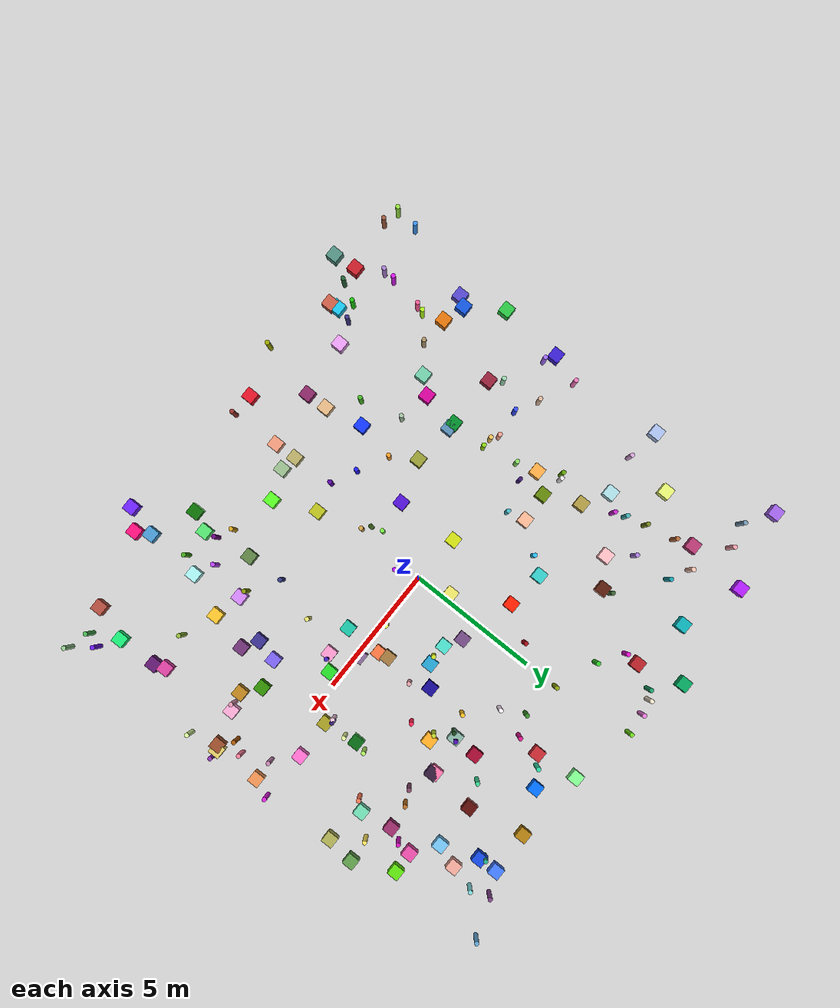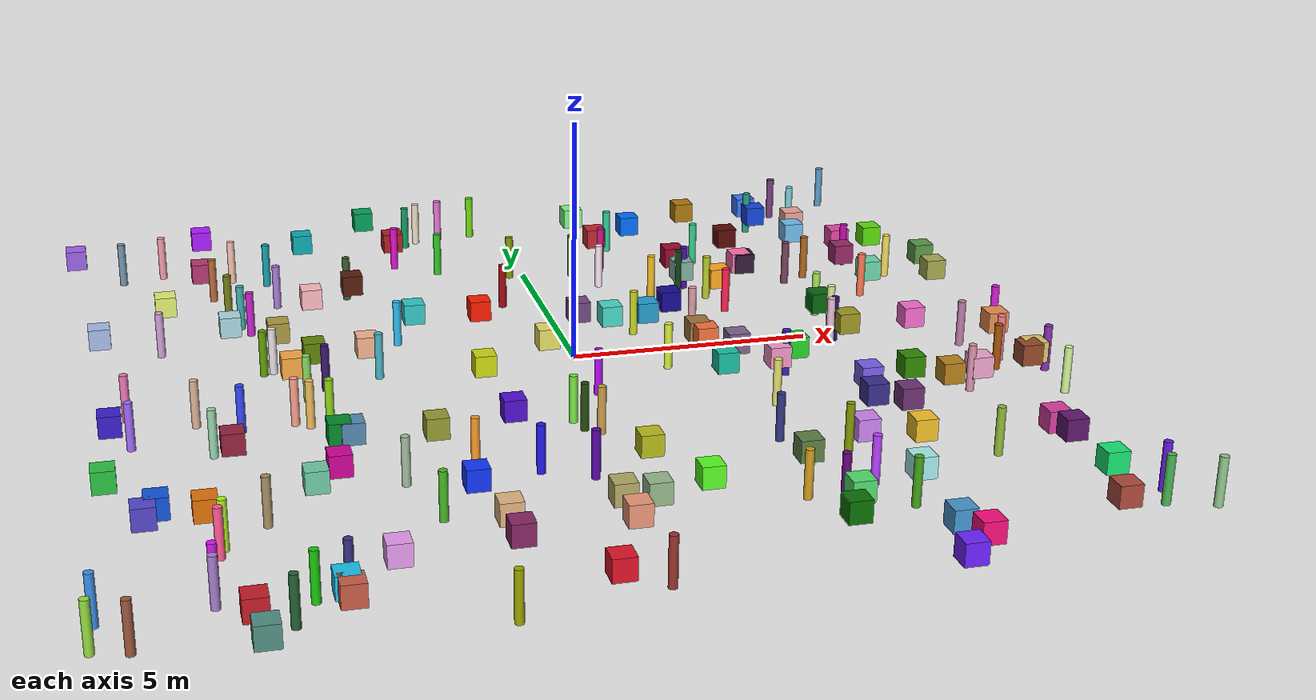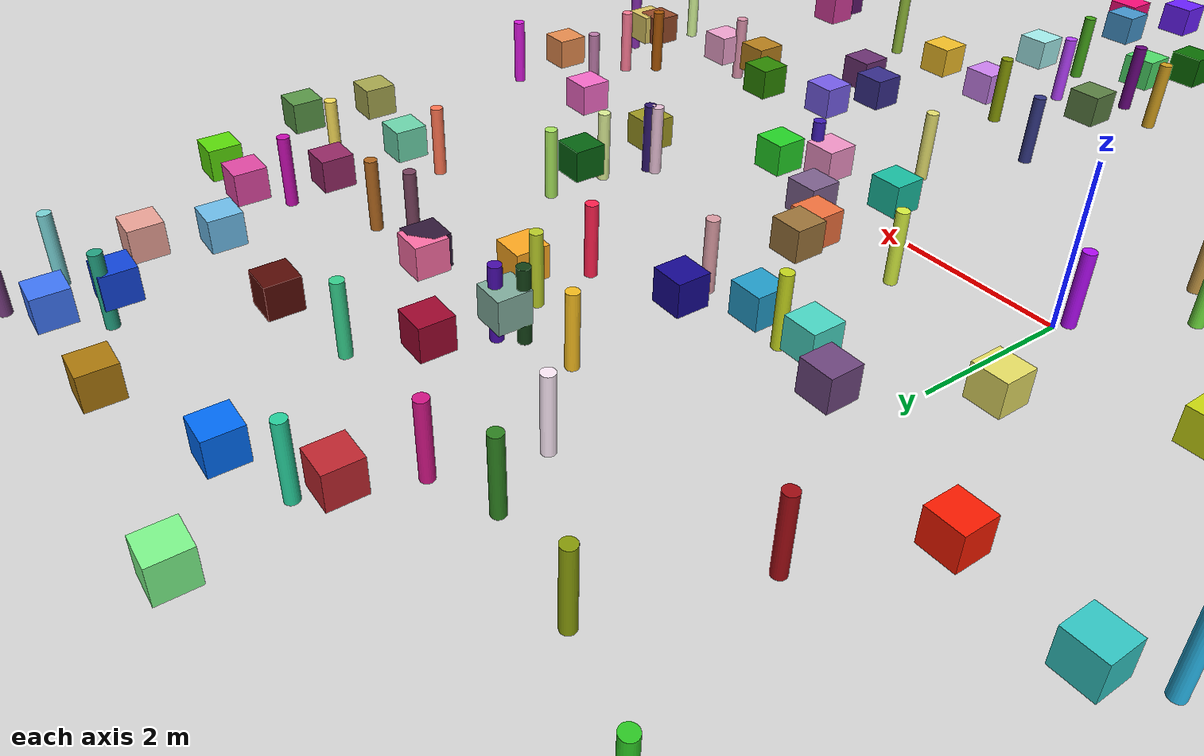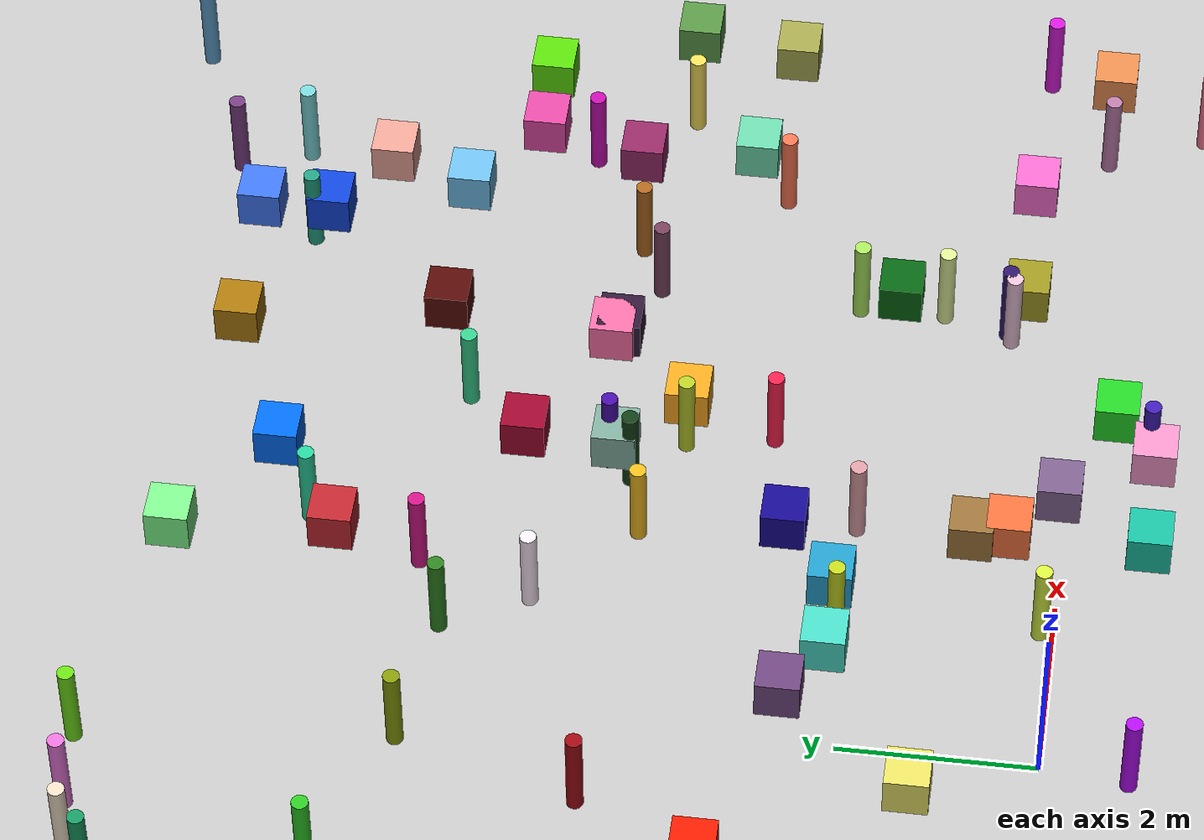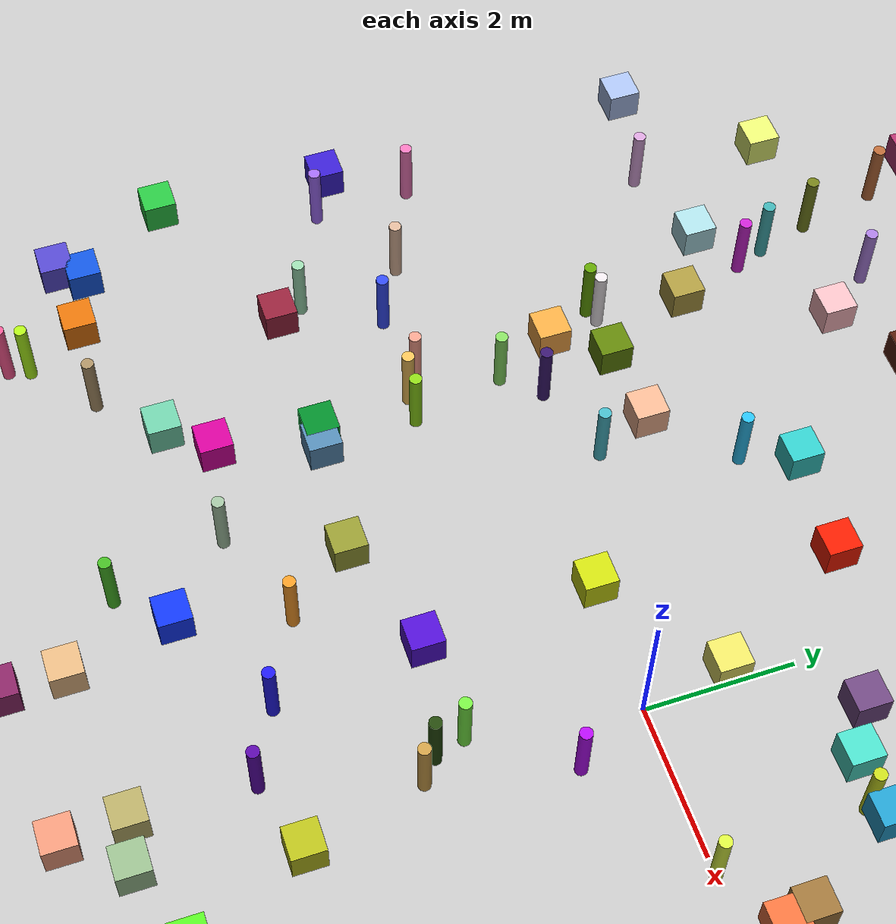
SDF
<?xml version='1.0' encoding='ASCII'?>
<sdf version='1.7'>
  <world name='warehouse'>
    <physics type="ode">
      <max_step_size>0.003</max_step_size>
      <real_time_factor>1.0</real_time_factor>
    </physics>
    <plugin name='ignition::gazebo::systems::Physics' filename='libignition-gazebo-physics-system.so'/>
    <plugin name='ignition::gazebo::systems::UserCommands' filename='libignition-gazebo-user-commands-system.so'/>
    <plugin name='ignition::gazebo::systems::SceneBroadcaster' filename='libignition-gazebo-scene-broadcaster-system.so'/>
    <plugin name="ignition::gazebo::systems::Sensors" filename="libignition-gazebo-sensors-system.so">
      <render_engine>ogre2</render_engine>
    </plugin>
    <plugin name="ignition::gazebo::systems::Imu" filename="libignition-gazebo-imu-system.so"/>
    <plugin name="ignition::gazebo::systems::NavSat" filename="libignition-gazebo-navsat-system.so"/>

    <scene>
      <ambient>1 1 1 1</ambient>
      <background>0 0 0 1</background>
      <shadows>0</shadows>
      <grid>false</grid>
    </scene>

    <spherical_coordinates>
      <surface_model>EARTH_WGS84</surface_model>
      <world_frame_orientation>ENU</world_frame_orientation>
      <latitude_deg>-22.986687</latitude_deg>
      <longitude_deg>-43.202501</longitude_deg>
      <elevation>0</elevation>
      <heading_deg>0</heading_deg>
    </spherical_coordinates>

    <model name='ground_plane'>
      <static>true</static>
      <link name='link'>
        <collision name='collision'>
          <geometry>
            <plane>
              <normal>0.0 0.0 1</normal>
              <size>1 1</size>
            </plane>
          </geometry>
        </collision>
      </link>
      <pose>0 0 0 0 0 0</pose>
    </model>

    <model name='unit_box_0'>
      <static>true</static>
      <pose>3.54 0.08 0 0 0 0</pose>
      <link name='link'>
        <collision name='collision'>
          <geometry>
            <box>
              <size>0.450000 0.450000 0.450000</size>
            </box>
          </geometry>
          <max_contacts>10</max_contacts>
        </collision>
        <visual name='visual'>
          <geometry>
            <box>
              <size>0.450000 0.450000 0.450000</size>
            </box>
          </geometry>
          <material>
            <ambient>0.49221642949295763 0.3819438212654387 0.5555495247401226 1</ambient>
            <diffuse>0.49221642949295763 0.3819438212654387 0.5555495247401226 1</diffuse>
            <script>
              <uri>file://media/materials/scripts/gazebo.material</uri>
              <name>Gazebo/RandomColor0</name>
            </script>
          </material>
        </visual>
      </link>
    </model>

    <model name='unit_cylinder_0'>
      <static>true</static>
      <pose>7.64 8.49 0 0 0 0</pose>
      <link name='link'>
        <collision name='collision'>
          <geometry>
            <cylinder>
              <radius>0.085000</radius>
              <length>1.000000</length>
            </cylinder>
          </geometry>
          <max_contacts>10</max_contacts>
        </collision>
        <visual name='visual'>
          <geometry>
            <cylinder>
              <radius>0.085000</radius>
              <length>1.000000</length>
            </cylinder>
          </geometry>
          <material>
            <ambient>0.46999343141526606 0.8260828982323868 0.8352996706723781 1</ambient>
            <diffuse>0.46999343141526606 0.8260828982323868 0.8352996706723781 1</diffuse>
            <script>
              <uri>file://media/materials/scripts/gazebo.material</uri>
              <name>Gazebo/RandomColor0</name>
            </script>
          </material>
        </visual>
      </link>
    </model>

    <model name='unit_box_1'>
      <static>true</static>
      <pose>7.68 4.87 0 0 0 0</pose>
      <link name='link'>
        <collision name='collision'>
          <geometry>
            <box>
              <size>0.450000 0.450000 0.450000</size>
            </box>
          </geometry>
          <max_contacts>10</max_contacts>
        </collision>
        <visual name='visual'>
          <geometry>
            <box>
              <size>0.450000 0.450000 0.450000</size>
            </box>
          </geometry>
          <material>
            <ambient>0.5787854574326788 0.1576126436969516 0.39572108881065005 1</ambient>
            <diffuse>0.5787854574326788 0.1576126436969516 0.39572108881065005 1</diffuse>
            <script>
              <uri>file://media/materials/scripts/gazebo.material</uri>
              <name>Gazebo/RandomColor1</name>
            </script>
          </material>
        </visual>
      </link>
    </model>

    <model name='unit_cylinder_1'>
      <static>true</static>
      <pose>3.65 -2.23 0 0 0 0</pose>
      <link name='link'>
        <collision name='collision'>
          <geometry>
            <cylinder>
              <radius>0.085000</radius>
              <length>1.000000</length>
            </cylinder>
          </geometry>
          <max_contacts>10</max_contacts>
        </collision>
        <visual name='visual'>
          <geometry>
            <cylinder>
              <radius>0.085000</radius>
              <length>1.000000</length>
            </cylinder>
          </geometry>
          <material>
            <ambient>0.8941086389998453 0.8734883737843444 0.4283232279845307 1</ambient>
            <diffuse>0.8941086389998453 0.8734883737843444 0.4283232279845307 1</diffuse>
            <script>
              <uri>file://media/materials/scripts/gazebo.material</uri>
              <name>Gazebo/RandomColor1</name>
            </script>
          </material>
        </visual>
      </link>
    </model>

    <model name='unit_box_2'>
      <static>true</static>
      <pose>4.67 -0.42 0 0 0 0</pose>
      <link name='link'>
        <collision name='collision'>
          <geometry>
            <box>
              <size>0.450000 0.450000 0.450000</size>
            </box>
          </geometry>
          <max_contacts>10</max_contacts>
        </collision>
        <visual name='visual'>
          <geometry>
            <box>
              <size>0.450000 0.450000 0.450000</size>
            </box>
          </geometry>
          <material>
            <ambient>0.14121589085153485 0.8244892088663838 0.14899712349563088 1</ambient>
            <diffuse>0.14121589085153485 0.8244892088663838 0.14899712349563088 1</diffuse>
            <script>
              <uri>file://media/materials/scripts/gazebo.material</uri>
              <name>Gazebo/RandomColor2</name>
            </script>
          </material>
        </visual>
      </link>
    </model>

    <model name='unit_cylinder_2'>
      <static>true</static>
      <pose>7.58 3.3 0 0 0 0</pose>
      <link name='link'>
        <collision name='collision'>
          <geometry>
            <cylinder>
              <radius>0.085000</radius>
              <length>1.000000</length>
            </cylinder>
          </geometry>
          <max_contacts>10</max_contacts>
        </collision>
        <visual name='visual'>
          <geometry>
            <cylinder>
              <radius>0.085000</radius>
              <length>1.000000</length>
            </cylinder>
          </geometry>
          <material>
            <ambient>0.994603734721729 0.4599668836425649 0.32006689947135913 1</ambient>
            <diffuse>0.994603734721729 0.4599668836425649 0.32006689947135913 1</diffuse>
            <script>
              <uri>file://media/materials/scripts/gazebo.material</uri>
              <name>Gazebo/RandomColor2</name>
            </script>
          </material>
        </visual>
      </link>
    </model>

    <model name='unit_box_3'>
      <static>true</static>
      <pose>-4.87 -7.57 0 0 0 0</pose>
      <link name='link'>
        <collision name='collision'>
          <geometry>
            <box>
              <size>0.450000 0.450000 0.450000</size>
            </box>
          </geometry>
          <max_contacts>10</max_contacts>
        </collision>
        <visual name='visual'>
          <geometry>
            <box>
              <size>0.450000 0.450000 0.450000</size>
            </box>
          </geometry>
          <material>
            <ambient>0.9026699777784415 0.6019357875675326 0.936818170479005 1</ambient>
            <diffuse>0.9026699777784415 0.6019357875675326 0.936818170479005 1</diffuse>
            <script>
              <uri>file://media/materials/scripts/gazebo.material</uri>
              <name>Gazebo/RandomColor3</name>
            </script>
          </material>
        </visual>
      </link>
    </model>

    <model name='unit_cylinder_3'>
      <static>true</static>
      <pose>-0.12 -2.75 0 0 0 0</pose>
      <link name='link'>
        <collision name='collision'>
          <geometry>
            <cylinder>
              <radius>0.085000</radius>
              <length>1.000000</length>
            </cylinder>
          </geometry>
          <max_contacts>10</max_contacts>
        </collision>
        <visual name='visual'>
          <geometry>
            <cylinder>
              <radius>0.085000</radius>
              <length>1.000000</length>
            </cylinder>
          </geometry>
          <material>
            <ambient>0.7898262252167743 0.6124958252999348 0.2808378183170157 1</ambient>
            <diffuse>0.7898262252167743 0.6124958252999348 0.2808378183170157 1</diffuse>
            <script>
              <uri>file://media/materials/scripts/gazebo.material</uri>
              <name>Gazebo/RandomColor3</name>
            </script>
          </material>
        </visual>
      </link>
    </model>

    <model name='unit_box_4'>
      <static>true</static>
      <pose>-2.74 -6.52 0 0 0 0</pose>
      <link name='link'>
        <collision name='collision'>
          <geometry>
            <box>
              <size>0.450000 0.450000 0.450000</size>
            </box>
          </geometry>
          <max_contacts>10</max_contacts>
        </collision>
        <visual name='visual'>
          <geometry>
            <box>
              <size>0.450000 0.450000 0.450000</size>
            </box>
          </geometry>
          <material>
            <ambient>0.8758270074759532 0.7026170182139044 0.4998424159085938 1</ambient>
            <diffuse>0.8758270074759532 0.7026170182139044 0.4998424159085938 1</diffuse>
            <script>
              <uri>file://media/materials/scripts/gazebo.material</uri>
              <name>Gazebo/RandomColor4</name>
            </script>
          </material>
        </visual>
      </link>
    </model>

    <model name='unit_cylinder_4'>
      <static>true</static>
      <pose>-0.59 4.47 0 0 0 0</pose>
      <link name='link'>
        <collision name='collision'>
          <geometry>
            <cylinder>
              <radius>0.085000</radius>
              <length>1.000000</length>
            </cylinder>
          </geometry>
          <max_contacts>10</max_contacts>
        </collision>
        <visual name='visual'>
          <geometry>
            <cylinder>
              <radius>0.085000</radius>
              <length>1.000000</length>
            </cylinder>
          </geometry>
          <material>
            <ambient>0.6235357225068702 0.041976520675021445 0.07086196109194554 1</ambient>
            <diffuse>0.6235357225068702 0.041976520675021445 0.07086196109194554 1</diffuse>
            <script>
              <uri>file://media/materials/scripts/gazebo.material</uri>
              <name>Gazebo/RandomColor4</name>
            </script>
          </material>
        </visual>
      </link>
    </model>

    <model name='unit_box_5'>
      <static>true</static>
      <pose>-9.95 8.63 0 0 0 0</pose>
      <link name='link'>
        <collision name='collision'>
          <geometry>
            <box>
              <size>0.450000 0.450000 0.450000</size>
            </box>
          </geometry>
          <max_contacts>10</max_contacts>
        </collision>
        <visual name='visual'>
          <geometry>
            <box>
              <size>0.450000 0.450000 0.450000</size>
            </box>
          </geometry>
          <material>
            <ambient>0.6154407336690317 0.37871564435809457 0.8966991050255034 1</ambient>
            <diffuse>0.6154407336690317 0.37871564435809457 0.8966991050255034 1</diffuse>
            <script>
              <uri>file://media/materials/scripts/gazebo.material</uri>
              <name>Gazebo/RandomColor5</name>
            </script>
          </material>
        </visual>
      </link>
    </model>

    <model name='unit_cylinder_5'>
      <static>true</static>
      <pose>0.29 -0.88 0 0 0 0</pose>
      <link name='link'>
        <collision name='collision'>
          <geometry>
            <cylinder>
              <radius>0.085000</radius>
              <length>1.000000</length>
            </cylinder>
          </geometry>
          <max_contacts>10</max_contacts>
        </collision>
        <visual name='visual'>
          <geometry>
            <cylinder>
              <radius>0.085000</radius>
              <length>1.000000</length>
            </cylinder>
          </geometry>
          <material>
            <ambient>0.6969958411022015 0.046907660404184814 0.953249913119854 1</ambient>
            <diffuse>0.6969958411022015 0.046907660404184814 0.953249913119854 1</diffuse>
            <script>
              <uri>file://media/materials/scripts/gazebo.material</uri>
              <name>Gazebo/RandomColor5</name>
            </script>
          </material>
        </visual>
      </link>
    </model>

    <model name='unit_box_6'>
      <static>true</static>
      <pose>7.36 7.51 0 0 0 0</pose>
      <link name='link'>
        <collision name='collision'>
          <geometry>
            <box>
              <size>0.450000 0.450000 0.450000</size>
            </box>
          </geometry>
          <max_contacts>10</max_contacts>
        </collision>
        <visual name='visual'>
          <geometry>
            <box>
              <size>0.450000 0.450000 0.450000</size>
            </box>
          </geometry>
          <material>
            <ambient>0.9200013658917384 0.6377764935082382 0.5884827738635453 1</ambient>
            <diffuse>0.9200013658917384 0.6377764935082382 0.5884827738635453 1</diffuse>
            <script>
              <uri>file://media/materials/scripts/gazebo.material</uri>
              <name>Gazebo/RandomColor6</name>
            </script>
          </material>
        </visual>
      </link>
    </model>

    <model name='unit_cylinder_6'>
      <static>true</static>
      <pose>-5.66 7.11 0 0 0 0</pose>
      <link name='link'>
        <collision name='collision'>
          <geometry>
            <cylinder>
              <radius>0.085000</radius>
              <length>1.000000</length>
            </cylinder>
          </geometry>
          <max_contacts>10</max_contacts>
        </collision>
        <visual name='visual'>
          <geometry>
            <cylinder>
              <radius>0.085000</radius>
              <length>1.000000</length>
            </cylinder>
          </geometry>
          <material>
            <ambient>0.08741391046455294 0.6259474203483671 0.6802748635079271 1</ambient>
            <diffuse>0.08741391046455294 0.6259474203483671 0.6802748635079271 1</diffuse>
            <script>
              <uri>file://media/materials/scripts/gazebo.material</uri>
              <name>Gazebo/RandomColor6</name>
            </script>
          </material>
        </visual>
      </link>
    </model>

    <model name='unit_box_7'>
      <static>true</static>
      <pose>3.29 8.06 0 0 0 0</pose>
      <link name='link'>
        <collision name='collision'>
          <geometry>
            <box>
              <size>0.450000 0.450000 0.450000</size>
            </box>
          </geometry>
          <max_contacts>10</max_contacts>
        </collision>
        <visual name='visual'>
          <geometry>
            <box>
              <size>0.450000 0.450000 0.450000</size>
            </box>
          </geometry>
          <material>
            <ambient>0.0008061066065178091 0.4221810701152692 0.9668438875156476 1</ambient>
            <diffuse>0.0008061066065178091 0.4221810701152692 0.9668438875156476 1</diffuse>
            <script>
              <uri>file://media/materials/scripts/gazebo.material</uri>
              <name>Gazebo/RandomColor7</name>
            </script>
          </material>
        </visual>
      </link>
    </model>

    <model name='unit_cylinder_7'>
      <static>true</static>
      <pose>2.06 0.14 0 0 0 0</pose>
      <link name='link'>
        <collision name='collision'>
          <geometry>
            <cylinder>
              <radius>0.085000</radius>
              <length>1.000000</length>
            </cylinder>
          </geometry>
          <max_contacts>10</max_contacts>
        </collision>
        <visual name='visual'>
          <geometry>
            <cylinder>
              <radius>0.085000</radius>
              <length>1.000000</length>
            </cylinder>
          </geometry>
          <material>
            <ambient>0.83487229274006 0.9308624301170804 0.2489823457315793 1</ambient>
            <diffuse>0.83487229274006 0.9308624301170804 0.2489823457315793 1</diffuse>
            <script>
              <uri>file://media/materials/scripts/gazebo.material</uri>
              <name>Gazebo/RandomColor7</name>
            </script>
          </material>
        </visual>
      </link>
    </model>

    <model name='unit_box_8'>
      <static>true</static>
      <pose>-2.82 3.35 0 0 0 0</pose>
      <link name='link'>
        <collision name='collision'>
          <geometry>
            <box>
              <size>0.450000 0.450000 0.450000</size>
            </box>
          </geometry>
          <max_contacts>10</max_contacts>
        </collision>
        <visual name='visual'>
          <geometry>
            <box>
              <size>0.450000 0.450000 0.450000</size>
            </box>
          </geometry>
          <material>
            <ambient>0.19632608082391967 0.7800212030862693 0.7700812796265892 1</ambient>
            <diffuse>0.19632608082391967 0.7800212030862693 0.7700812796265892 1</diffuse>
            <script>
              <uri>file://media/materials/scripts/gazebo.material</uri>
              <name>Gazebo/RandomColor8</name>
            </script>
          </material>
        </visual>
      </link>
    </model>

    <model name='unit_cylinder_8'>
      <static>true</static>
      <pose>-2.58 7.6 0 0 0 0</pose>
      <link name='link'>
        <collision name='collision'>
          <geometry>
            <cylinder>
              <radius>0.085000</radius>
              <length>1.000000</length>
            </cylinder>
          </geometry>
          <max_contacts>10</max_contacts>
        </collision>
        <visual name='visual'>
          <geometry>
            <cylinder>
              <radius>0.085000</radius>
              <length>1.000000</length>
            </cylinder>
          </geometry>
          <material>
            <ambient>0.8731148797888116 0.05048151335118567 0.7935635113024313 1</ambient>
            <diffuse>0.8731148797888116 0.05048151335118567 0.7935635113024313 1</diffuse>
            <script>
              <uri>file://media/materials/scripts/gazebo.material</uri>
              <name>Gazebo/RandomColor8</name>
            </script>
          </material>
        </visual>
      </link>
    </model>

    <model name='unit_box_9'>
      <static>true</static>
      <pose>6.55 8.07 0 0 0 0</pose>
      <link name='link'>
        <collision name='collision'>
          <geometry>
            <box>
              <size>0.450000 0.450000 0.450000</size>
            </box>
          </geometry>
          <max_contacts>10</max_contacts>
        </collision>
        <visual name='visual'>
          <geometry>
            <box>
              <size>0.450000 0.450000 0.450000</size>
            </box>
          </geometry>
          <material>
            <ambient>0.06638551337313603 0.2678031365858804 0.8557967761337132 1</ambient>
            <diffuse>0.06638551337313603 0.2678031365858804 0.8557967761337132 1</diffuse>
            <script>
              <uri>file://media/materials/scripts/gazebo.material</uri>
              <name>Gazebo/RandomColor9</name>
            </script>
          </material>
        </visual>
      </link>
    </model>

    <model name='unit_cylinder_9'>
      <static>true</static>
      <pose>-7.95 -7.96 0 0 0 0</pose>
      <link name='link'>
        <collision name='collision'>
          <geometry>
            <cylinder>
              <radius>0.085000</radius>
              <length>1.000000</length>
            </cylinder>
          </geometry>
          <max_contacts>10</max_contacts>
        </collision>
        <visual name='visual'>
          <geometry>
            <cylinder>
              <radius>0.085000</radius>
              <length>1.000000</length>
            </cylinder>
          </geometry>
          <material>
            <ambient>0.6398860359785785 0.4799973726306034 0.7931210935479871 1</ambient>
            <diffuse>0.6398860359785785 0.4799973726306034 0.7931210935479871 1</diffuse>
            <script>
              <uri>file://media/materials/scripts/gazebo.material</uri>
              <name>Gazebo/RandomColor9</name>
            </script>
          </material>
        </visual>
      </link>
    </model>

    <model name='unit_box_10'>
      <static>true</static>
      <pose>-1.76 -2.22 0 0 0 0</pose>
      <link name='link'>
        <collision name='collision'>
          <geometry>
            <box>
              <size>0.450000 0.450000 0.450000</size>
            </box>
          </geometry>
          <max_contacts>10</max_contacts>
        </collision>
        <visual name='visual'>
          <geometry>
            <box>
              <size>0.450000 0.450000 0.450000</size>
            </box>
          </geometry>
          <material>
            <ambient>0.30819914242388124 0.05641024999295219 0.8069949057750591 1</ambient>
            <diffuse>0.30819914242388124 0.05641024999295219 0.8069949057750591 1</diffuse>
            <script>
              <uri>file://media/materials/scripts/gazebo.material</uri>
              <name>Gazebo/RandomColor10</name>
            </script>
          </material>
        </visual>
      </link>
    </model>

    <model name='unit_cylinder_10'>
      <static>true</static>
      <pose>-6.33 -8.14 0 0 0 0</pose>
      <link name='link'>
        <collision name='collision'>
          <geometry>
            <cylinder>
              <radius>0.085000</radius>
              <length>1.000000</length>
            </cylinder>
          </geometry>
          <max_contacts>10</max_contacts>
        </collision>
        <visual name='visual'>
          <geometry>
            <cylinder>
              <radius>0.085000</radius>
              <length>1.000000</length>
            </cylinder>
          </geometry>
          <material>
            <ambient>0.09806367104197622 0.7730669275351795 0.04683629350049412 1</ambient>
            <diffuse>0.09806367104197622 0.7730669275351795 0.04683629350049412 1</diffuse>
            <script>
              <uri>file://media/materials/scripts/gazebo.material</uri>
              <name>Gazebo/RandomColor10</name>
            </script>
          </material>
        </visual>
      </link>
    </model>

    <model name='unit_box_11'>
      <static>true</static>
      <pose>-9.44 -1.17 0 0 0 0</pose>
      <link name='link'>
        <collision name='collision'>
          <geometry>
            <box>
              <size>0.450000 0.450000 0.450000</size>
            </box>
          </geometry>
          <max_contacts>10</max_contacts>
        </collision>
        <visual name='visual'>
          <geometry>
            <box>
              <size>0.450000 0.450000 0.450000</size>
            </box>
          </geometry>
          <material>
            <ambient>0.2187403771791414 0.11308076702255188 0.7992289625326177 1</ambient>
            <diffuse>0.2187403771791414 0.11308076702255188 0.7992289625326177 1</diffuse>
            <script>
              <uri>file://media/materials/scripts/gazebo.material</uri>
              <name>Gazebo/RandomColor11</name>
            </script>
          </material>
        </visual>
      </link>
    </model>

    <model name='unit_cylinder_11'>
      <static>true</static>
      <pose>-6.04 1.77 0 0 0 0</pose>
      <link name='link'>
        <collision name='collision'>
          <geometry>
            <cylinder>
              <radius>0.085000</radius>
              <length>1.000000</length>
            </cylinder>
          </geometry>
          <max_contacts>10</max_contacts>
        </collision>
        <visual name='visual'>
          <geometry>
            <cylinder>
              <radius>0.085000</radius>
              <length>1.000000</length>
            </cylinder>
          </geometry>
          <material>
            <ambient>0.9034382308019122 0.878446810579239 0.8954639350832497 1</ambient>
            <diffuse>0.9034382308019122 0.878446810579239 0.8954639350832497 1</diffuse>
            <script>
              <uri>file://media/materials/scripts/gazebo.material</uri>
              <name>Gazebo/RandomColor11</name>
            </script>
          </material>
        </visual>
      </link>
    </model>

    <model name='unit_box_12'>
      <static>true</static>
      <pose>-6.78 3.5 0 0 0 0</pose>
      <link name='link'>
        <collision name='collision'>
          <geometry>
            <box>
              <size>0.450000 0.450000 0.450000</size>
            </box>
          </geometry>
          <max_contacts>10</max_contacts>
        </collision>
        <visual name='visual'>
          <geometry>
            <box>
              <size>0.450000 0.450000 0.450000</size>
            </box>
          </geometry>
          <material>
            <ambient>0.6623910014228391 0.8483054760047987 0.8784508396129014 1</ambient>
            <diffuse>0.6623910014228391 0.8483054760047987 0.8784508396129014 1</diffuse>
            <script>
              <uri>file://media/materials/scripts/gazebo.material</uri>
              <name>Gazebo/RandomColor12</name>
            </script>
          </material>
        </visual>
      </link>
    </model>

    <model name='unit_cylinder_12'>
      <static>true</static>
      <pose>2.66 7.65 0 0 0 0</pose>
      <link name='link'>
        <collision name='collision'>
          <geometry>
            <cylinder>
              <radius>0.085000</radius>
              <length>1.000000</length>
            </cylinder>
          </geometry>
          <max_contacts>10</max_contacts>
        </collision>
        <visual name='visual'>
          <geometry>
            <cylinder>
              <radius>0.085000</radius>
              <length>1.000000</length>
            </cylinder>
          </geometry>
          <material>
            <ambient>0.15143648891922623 0.8175906025052687 0.6141172141436677 1</ambient>
            <diffuse>0.15143648891922623 0.8175906025052687 0.6141172141436677 1</diffuse>
            <script>
              <uri>file://media/materials/scripts/gazebo.material</uri>
              <name>Gazebo/RandomColor12</name>
            </script>
          </material>
        </visual>
      </link>
    </model>

    <model name='unit_box_13'>
      <static>true</static>
      <pose>-5.85 -8.45 0 0 0 0</pose>
      <link name='link'>
        <collision name='collision'>
          <geometry>
            <box>
              <size>0.450000 0.450000 0.450000</size>
            </box>
          </geometry>
          <max_contacts>10</max_contacts>
        </collision>
        <visual name='visual'>
          <geometry>
            <box>
              <size>0.450000 0.450000 0.450000</size>
            </box>
          </geometry>
          <material>
            <ambient>0.0886331011918422 0.7603424364719541 0.9202413364235801 1</ambient>
            <diffuse>0.0886331011918422 0.7603424364719541 0.9202413364235801 1</diffuse>
            <script>
              <uri>file://media/materials/scripts/gazebo.material</uri>
              <name>Gazebo/RandomColor13</name>
            </script>
          </material>
        </visual>
      </link>
    </model>

    <model name='unit_cylinder_13'>
      <static>true</static>
      <pose>-3.23 -9.56 0 0 0 0</pose>
      <link name='link'>
        <collision name='collision'>
          <geometry>
            <cylinder>
              <radius>0.085000</radius>
              <length>1.000000</length>
            </cylinder>
          </geometry>
          <max_contacts>10</max_contacts>
        </collision>
        <visual name='visual'>
          <geometry>
            <cylinder>
              <radius>0.085000</radius>
              <length>1.000000</length>
            </cylinder>
          </geometry>
          <material>
            <ambient>0.5966252229411809 0.6408981784114667 0.001576873510488408 1</ambient>
            <diffuse>0.5966252229411809 0.6408981784114667 0.001576873510488408 1</diffuse>
            <script>
              <uri>file://media/materials/scripts/gazebo.material</uri>
              <name>Gazebo/RandomColor13</name>
            </script>
          </material>
        </visual>
      </link>
    </model>

    <model name='unit_box_14'>
      <static>true</static>
      <pose>8.28 -5.14 0 0 0 0</pose>
      <link name='link'>
        <collision name='collision'>
          <geometry>
            <box>
              <size>0.450000 0.450000 0.450000</size>
            </box>
          </geometry>
          <max_contacts>10</max_contacts>
        </collision>
        <visual name='visual'>
          <geometry>
            <box>
              <size>0.450000 0.450000 0.450000</size>
            </box>
          </geometry>
          <material>
            <ambient>0.8344831727208002 0.2399697383260848 0.6123536341076805 1</ambient>
            <diffuse>0.8344831727208002 0.2399697383260848 0.6123536341076805 1</diffuse>
            <script>
              <uri>file://media/materials/scripts/gazebo.material</uri>
              <name>Gazebo/RandomColor14</name>
            </script>
          </material>
        </visual>
      </link>
    </model>

    <model name='unit_cylinder_14'>
      <static>true</static>
      <pose>-3.27 2.74 0 0 0 0</pose>
      <link name='link'>
        <collision name='collision'>
          <geometry>
            <cylinder>
              <radius>0.085000</radius>
              <length>1.000000</length>
            </cylinder>
          </geometry>
          <max_contacts>10</max_contacts>
        </collision>
        <visual name='visual'>
          <geometry>
            <cylinder>
              <radius>0.085000</radius>
              <length>1.000000</length>
            </cylinder>
          </geometry>
          <material>
            <ambient>0.1616640995869777 0.7356496990827222 0.9365464673181627 1</ambient>
            <diffuse>0.1616640995869777 0.7356496990827222 0.9365464673181627 1</diffuse>
            <script>
              <uri>file://media/materials/scripts/gazebo.material</uri>
              <name>Gazebo/RandomColor14</name>
            </script>
          </material>
        </visual>
      </link>
    </model>

    <model name='unit_box_15'>
      <static>true</static>
      <pose>-1.38 3.21 0 0 0 0</pose>
      <link name='link'>
        <collision name='collision'>
          <geometry>
            <box>
              <size>0.450000 0.450000 0.450000</size>
            </box>
          </geometry>
          <max_contacts>10</max_contacts>
        </collision>
        <visual name='visual'>
          <geometry>
            <box>
              <size>0.450000 0.450000 0.450000</size>
            </box>
          </geometry>
          <material>
            <ambient>0.9789827987215421 0.10518219629356829 0.00033992939039728665 1</ambient>
            <diffuse>0.9789827987215421 0.10518219629356829 0.00033992939039728665 1</diffuse>
            <script>
              <uri>file://media/materials/scripts/gazebo.material</uri>
              <name>Gazebo/RandomColor15</name>
            </script>
          </material>
        </visual>
      </link>
    </model>

    <model name='unit_cylinder_15'>
      <static>true</static>
      <pose>5.9 0.76 0 0 0 0</pose>
      <link name='link'>
        <collision name='collision'>
          <geometry>
            <cylinder>
              <radius>0.085000</radius>
              <length>1.000000</length>
            </cylinder>
          </geometry>
          <max_contacts>10</max_contacts>
        </collision>
        <visual name='visual'>
          <geometry>
            <cylinder>
              <radius>0.085000</radius>
              <length>1.000000</length>
            </cylinder>
          </geometry>
          <material>
            <ambient>0.9063739285020391 0.7514042748669589 0.838011728663642 1</ambient>
            <diffuse>0.9063739285020391 0.7514042748669589 0.838011728663642 1</diffuse>
            <script>
              <uri>file://media/materials/scripts/gazebo.material</uri>
              <name>Gazebo/RandomColor15</name>
            </script>
          </material>
        </visual>
      </link>
    </model>

    <model name='unit_box_16'>
      <static>true</static>
      <pose>-7.37 -8.85 0 0 0 0</pose>
      <link name='link'>
        <collision name='collision'>
          <geometry>
            <box>
              <size>0.450000 0.450000 0.450000</size>
            </box>
          </geometry>
          <max_contacts>10</max_contacts>
        </collision>
        <visual name='visual'>
          <geometry>
            <box>
              <size>0.450000 0.450000 0.450000</size>
            </box>
          </geometry>
          <material>
            <ambient>0.7658787853236971 0.10682762159563586 0.15104276840093267 1</ambient>
            <diffuse>0.7658787853236971 0.10682762159563586 0.15104276840093267 1</diffuse>
            <script>
              <uri>file://media/materials/scripts/gazebo.material</uri>
              <name>Gazebo/RandomColor16</name>
            </script>
          </material>
        </visual>
      </link>
    </model>

    <model name='unit_cylinder_16'>
      <static>true</static>
      <pose>6.15 4.48 0 0 0 0</pose>
      <link name='link'>
        <collision name='collision'>
          <geometry>
            <cylinder>
              <radius>0.085000</radius>
              <length>1.000000</length>
            </cylinder>
          </geometry>
          <max_contacts>10</max_contacts>
        </collision>
        <visual name='visual'>
          <geometry>
            <cylinder>
              <radius>0.085000</radius>
              <length>1.000000</length>
            </cylinder>
          </geometry>
          <material>
            <ambient>0.4622271195110065 0.2528442664038917 0.36049144175780334 1</ambient>
            <diffuse>0.4622271195110065 0.2528442664038917 0.36049144175780334 1</diffuse>
            <script>
              <uri>file://media/materials/scripts/gazebo.material</uri>
              <name>Gazebo/RandomColor16</name>
            </script>
          </material>
        </visual>
      </link>
    </model>

    <model name='unit_box_17'>
      <static>true</static>
      <pose>-1.36 -8.92 0 0 0 0</pose>
      <link name='link'>
        <collision name='collision'>
          <geometry>
            <box>
              <size>0.450000 0.450000 0.450000</size>
            </box>
          </geometry>
          <max_contacts>10</max_contacts>
        </collision>
        <visual name='visual'>
          <geometry>
            <box>
              <size>0.450000 0.450000 0.450000</size>
            </box>
          </geometry>
          <material>
            <ambient>0.8711556283389497 0.07227653963872849 0.15338370299610837 1</ambient>
            <diffuse>0.8711556283389497 0.07227653963872849 0.15338370299610837 1</diffuse>
            <script>
              <uri>file://media/materials/scripts/gazebo.material</uri>
              <name>Gazebo/RandomColor17</name>
            </script>
          </material>
        </visual>
      </link>
    </model>

    <model name='unit_cylinder_17'>
      <static>true</static>
      <pose>2.82 -6.39 0 0 0 0</pose>
      <link name='link'>
        <collision name='collision'>
          <geometry>
            <cylinder>
              <radius>0.085000</radius>
              <length>1.000000</length>
            </cylinder>
          </geometry>
          <max_contacts>10</max_contacts>
        </collision>
        <visual name='visual'>
          <geometry>
            <cylinder>
              <radius>0.085000</radius>
              <length>1.000000</length>
            </cylinder>
          </geometry>
          <material>
            <ambient>0.819102408019355 0.6173032143909429 0.11231297093222081 1</ambient>
            <diffuse>0.819102408019355 0.6173032143909429 0.11231297093222081 1</diffuse>
            <script>
              <uri>file://media/materials/scripts/gazebo.material</uri>
              <name>Gazebo/RandomColor17</name>
            </script>
          </material>
        </visual>
      </link>
    </model>

    <model name='unit_box_18'>
      <static>true</static>
      <pose>7.71 0.66 0 0 0 0</pose>
      <link name='link'>
        <collision name='collision'>
          <geometry>
            <box>
              <size>0.450000 0.450000 0.450000</size>
            </box>
          </geometry>
          <max_contacts>10</max_contacts>
        </collision>
        <visual name='visual'>
          <geometry>
            <box>
              <size>0.450000 0.450000 0.450000</size>
            </box>
          </geometry>
          <material>
            <ambient>0.9665622435585168 0.41716344496851265 0.789984054476536 1</ambient>
            <diffuse>0.9665622435585168 0.41716344496851265 0.789984054476536 1</diffuse>
            <script>
              <uri>file://media/materials/scripts/gazebo.material</uri>
              <name>Gazebo/RandomColor18</name>
            </script>
          </material>
        </visual>
      </link>
    </model>

    <model name='unit_cylinder_18'>
      <static>true</static>
      <pose>4.61 -7.14 0 0 0 0</pose>
      <link name='link'>
        <collision name='collision'>
          <geometry>
            <cylinder>
              <radius>0.085000</radius>
              <length>1.000000</length>
            </cylinder>
          </geometry>
          <max_contacts>10</max_contacts>
        </collision>
        <visual name='visual'>
          <geometry>
            <cylinder>
              <radius>0.085000</radius>
              <length>1.000000</length>
            </cylinder>
          </geometry>
          <material>
            <ambient>0.2592761966020771 0.6384268163339042 0.09613030569205283 1</ambient>
            <diffuse>0.2592761966020771 0.6384268163339042 0.09613030569205283 1</diffuse>
            <script>
              <uri>file://media/materials/scripts/gazebo.material</uri>
              <name>Gazebo/RandomColor18</name>
            </script>
          </material>
        </visual>
      </link>
    </model>

    <model name='unit_box_19'>
      <static>true</static>
      <pose>-3.02 9.9 0 0 0 0</pose>
      <link name='link'>
        <collision name='collision'>
          <geometry>
            <box>
              <size>0.450000 0.450000 0.450000</size>
            </box>
          </geometry>
          <max_contacts>10</max_contacts>
        </collision>
        <visual name='visual'>
          <geometry>
            <box>
              <size>0.450000 0.450000 0.450000</size>
            </box>
          </geometry>
          <material>
            <ambient>0.004717150632328471 0.6250235168678344 0.3515729885520935 1</ambient>
            <diffuse>0.004717150632328471 0.6250235168678344 0.3515729885520935 1</diffuse>
            <script>
              <uri>file://media/materials/scripts/gazebo.material</uri>
              <name>Gazebo/RandomColor19</name>
            </script>
          </material>
        </visual>
      </link>
    </model>

    <model name='unit_cylinder_19'>
      <static>true</static>
      <pose>-2.09 9.05 0 0 0 0</pose>
      <link name='link'>
        <collision name='collision'>
          <geometry>
            <cylinder>
              <radius>0.085000</radius>
              <length>1.000000</length>
            </cylinder>
          </geometry>
          <max_contacts>10</max_contacts>
        </collision>
        <visual name='visual'>
          <geometry>
            <cylinder>
              <radius>0.085000</radius>
              <length>1.000000</length>
            </cylinder>
          </geometry>
          <material>
            <ambient>0.07983190309297217 0.6005276894350505 0.38091359060201324 1</ambient>
            <diffuse>0.07983190309297217 0.6005276894350505 0.38091359060201324 1</diffuse>
            <script>
              <uri>file://media/materials/scripts/gazebo.material</uri>
              <name>Gazebo/RandomColor19</name>
            </script>
          </material>
        </visual>
      </link>
    </model>

    <model name='unit_box_20'>
      <static>true</static>
      <pose>-0.62 -6.25 0 0 0 0</pose>
      <link name='link'>
        <collision name='collision'>
          <geometry>
            <box>
              <size>0.450000 0.450000 0.450000</size>
            </box>
          </geometry>
          <max_contacts>10</max_contacts>
        </collision>
        <visual name='visual'>
          <geometry>
            <box>
              <size>0.450000 0.450000 0.450000</size>
            </box>
          </geometry>
          <material>
            <ambient>0.6995548471565017 0.6582530707848234 0.3927673776314795 1</ambient>
            <diffuse>0.6995548471565017 0.6582530707848234 0.3927673776314795 1</diffuse>
            <script>
              <uri>file://media/materials/scripts/gazebo.material</uri>
              <name>Gazebo/RandomColor20</name>
            </script>
          </material>
        </visual>
      </link>
    </model>

    <model name='unit_cylinder_20'>
      <static>true</static>
      <pose>-7.93 -7.52 0 0 0 0</pose>
      <link name='link'>
        <collision name='collision'>
          <geometry>
            <cylinder>
              <radius>0.085000</radius>
              <length>1.000000</length>
            </cylinder>
          </geometry>
          <max_contacts>10</max_contacts>
        </collision>
        <visual name='visual'>
          <geometry>
            <cylinder>
              <radius>0.085000</radius>
              <length>1.000000</length>
            </cylinder>
          </geometry>
          <material>
            <ambient>0.8195183544858631 0.08890003333785146 0.9104346134078853 1</ambient>
            <diffuse>0.8195183544858631 0.08890003333785146 0.9104346134078853 1</diffuse>
            <script>
              <uri>file://media/materials/scripts/gazebo.material</uri>
              <name>Gazebo/RandomColor20</name>
            </script>
          </material>
        </visual>
      </link>
    </model>

    <model name='unit_box_21'>
      <static>true</static>
      <pose>4.14 -0.84 0 0 0 0</pose>
      <link name='link'>
        <collision name='collision'>
          <geometry>
            <box>
              <size>0.450000 0.450000 0.450000</size>
            </box>
          </geometry>
          <max_contacts>10</max_contacts>
        </collision>
        <visual name='visual'>
          <geometry>
            <box>
              <size>0.450000 0.450000 0.450000</size>
            </box>
          </geometry>
          <material>
            <ambient>0.94493098200949 0.5805900964786412 0.7797267321622182 1</ambient>
            <diffuse>0.94493098200949 0.5805900964786412 0.7797267321622182 1</diffuse>
            <script>
              <uri>file://media/materials/scripts/gazebo.material</uri>
              <name>Gazebo/RandomColor21</name>
            </script>
          </material>
        </visual>
      </link>
    </model>

    <model name='unit_cylinder_21'>
      <static>true</static>
      <pose>-0.5 -9.01 0 0 0 0</pose>
      <link name='link'>
        <collision name='collision'>
          <geometry>
            <cylinder>
              <radius>0.085000</radius>
              <length>1.000000</length>
            </cylinder>
          </geometry>
          <max_contacts>10</max_contacts>
        </collision>
        <visual name='visual'>
          <geometry>
            <cylinder>
              <radius>0.085000</radius>
              <length>1.000000</length>
            </cylinder>
          </geometry>
          <material>
            <ambient>0.5935503974926962 0.1981231207876929 0.1723133132744028 1</ambient>
            <diffuse>0.5935503974926962 0.1981231207876929 0.1723133132744028 1</diffuse>
            <script>
              <uri>file://media/materials/scripts/gazebo.material</uri>
              <name>Gazebo/RandomColor21</name>
            </script>
          </material>
        </visual>
      </link>
    </model>

    <model name='unit_box_22'>
      <static>true</static>
      <pose>3.17 -7.86 0 0 0 0</pose>
      <link name='link'>
        <collision name='collision'>
          <geometry>
            <box>
              <size>0.450000 0.450000 0.450000</size>
            </box>
          </geometry>
          <max_contacts>10</max_contacts>
        </collision>
        <visual name='visual'>
          <geometry>
            <box>
              <size>0.450000 0.450000 0.450000</size>
            </box>
          </geometry>
          <material>
            <ambient>0.042180342107623 0.4331906733586902 0.01565587071072405 1</ambient>
            <diffuse>0.042180342107623 0.4331906733586902 0.01565587071072405 1</diffuse>
            <script>
              <uri>file://media/materials/scripts/gazebo.material</uri>
              <name>Gazebo/RandomColor22</name>
            </script>
          </material>
        </visual>
      </link>
    </model>

    <model name='unit_cylinder_22'>
      <static>true</static>
      <pose>3.42 -6.69 0 0 0 0</pose>
      <link name='link'>
        <collision name='collision'>
          <geometry>
            <cylinder>
              <radius>0.085000</radius>
              <length>1.000000</length>
            </cylinder>
          </geometry>
          <max_contacts>10</max_contacts>
        </collision>
        <visual name='visual'>
          <geometry>
            <cylinder>
              <radius>0.085000</radius>
              <length>1.000000</length>
            </cylinder>
          </geometry>
          <material>
            <ambient>0.40371749337117635 0.018035788357352645 0.4952989950266149 1</ambient>
            <diffuse>0.40371749337117635 0.018035788357352645 0.4952989950266149 1</diffuse>
            <script>
              <uri>file://media/materials/scripts/gazebo.material</uri>
              <name>Gazebo/RandomColor22</name>
            </script>
          </material>
        </visual>
      </link>
    </model>

    <model name='unit_box_23'>
      <static>true</static>
      <pose>5.38 -3.11 0 0 0 0</pose>
      <link name='link'>
        <collision name='collision'>
          <geometry>
            <box>
              <size>0.450000 0.450000 0.450000</size>
            </box>
          </geometry>
          <max_contacts>10</max_contacts>
        </collision>
        <visual name='visual'>
          <geometry>
            <box>
              <size>0.450000 0.450000 0.450000</size>
            </box>
          </geometry>
          <material>
            <ambient>0.21470545850147904 0.17822945384433364 0.5443195358824162 1</ambient>
            <diffuse>0.21470545850147904 0.17822945384433364 0.5443195358824162 1</diffuse>
            <script>
              <uri>file://media/materials/scripts/gazebo.material</uri>
              <name>Gazebo/RandomColor23</name>
            </script>
          </material>
        </visual>
      </link>
    </model>

    <model name='unit_cylinder_23'>
      <static>true</static>
      <pose>-9.9 -8.09 0 0 0 0</pose>
      <link name='link'>
        <collision name='collision'>
          <geometry>
            <cylinder>
              <radius>0.085000</radius>
              <length>1.000000</length>
            </cylinder>
          </geometry>
          <max_contacts>10</max_contacts>
        </collision>
        <visual name='visual'>
          <geometry>
            <cylinder>
              <radius>0.085000</radius>
              <length>1.000000</length>
            </cylinder>
          </geometry>
          <material>
            <ambient>0.22288324703453943 0.5596985518016837 0.9148220679438888 1</ambient>
            <diffuse>0.22288324703453943 0.5596985518016837 0.9148220679438888 1</diffuse>
            <script>
              <uri>file://media/materials/scripts/gazebo.material</uri>
              <name>Gazebo/RandomColor23</name>
            </script>
          </material>
        </visual>
      </link>
    </model>

    <model name='unit_box_24'>
      <static>true</static>
      <pose>1.1 -5.94 0 0 0 0</pose>
      <link name='link'>
        <collision name='collision'>
          <geometry>
            <box>
              <size>0.450000 0.450000 0.450000</size>
            </box>
          </geometry>
          <max_contacts>10</max_contacts>
        </collision>
        <visual name='visual'>
          <geometry>
            <box>
              <size>0.450000 0.450000 0.450000</size>
            </box>
          </geometry>
          <material>
            <ambient>0.33861427677319433 0.987256980340304 0.13684380857669165 1</ambient>
            <diffuse>0.33861427677319433 0.987256980340304 0.13684380857669165 1</diffuse>
            <script>
              <uri>file://media/materials/scripts/gazebo.material</uri>
              <name>Gazebo/RandomColor24</name>
            </script>
          </material>
        </visual>
      </link>
    </model>

    <model name='unit_cylinder_24'>
      <static>true</static>
      <pose>-7.74 -6.24 0 0 0 0</pose>
      <link name='link'>
        <collision name='collision'>
          <geometry>
            <cylinder>
              <radius>0.085000</radius>
              <length>1.000000</length>
            </cylinder>
          </geometry>
          <max_contacts>10</max_contacts>
        </collision>
        <visual name='visual'>
          <geometry>
            <cylinder>
              <radius>0.085000</radius>
              <length>1.000000</length>
            </cylinder>
          </geometry>
          <material>
            <ambient>0.9992332628684522 0.3465863657276286 0.5757859994032216 1</ambient>
            <diffuse>0.9992332628684522 0.3465863657276286 0.5757859994032216 1</diffuse>
            <script>
              <uri>file://media/materials/scripts/gazebo.material</uri>
              <name>Gazebo/RandomColor24</name>
            </script>
          </material>
        </visual>
      </link>
    </model>

    <model name='unit_box_25'>
      <static>true</static>
      <pose>-2.71 -7.34 0 0 0 0</pose>
      <link name='link'>
        <collision name='collision'>
          <geometry>
            <box>
              <size>0.450000 0.450000 0.450000</size>
            </box>
          </geometry>
          <max_contacts>10</max_contacts>
        </collision>
        <visual name='visual'>
          <geometry>
            <box>
              <size>0.450000 0.450000 0.450000</size>
            </box>
          </geometry>
          <material>
            <ambient>0.5207034857579925 0.14055315646117983 0.38648327738103294 1</ambient>
            <diffuse>0.5207034857579925 0.14055315646117983 0.38648327738103294 1</diffuse>
            <script>
              <uri>file://media/materials/scripts/gazebo.material</uri>
              <name>Gazebo/RandomColor25</name>
            </script>
          </material>
        </visual>
      </link>
    </model>

    <model name='unit_cylinder_25'>
      <static>true</static>
      <pose>1.86 5.27 0 0 0 0</pose>
      <link name='link'>
        <collision name='collision'>
          <geometry>
            <cylinder>
              <radius>0.085000</radius>
              <length>1.000000</length>
            </cylinder>
          </geometry>
          <max_contacts>10</max_contacts>
        </collision>
        <visual name='visual'>
          <geometry>
            <cylinder>
              <radius>0.085000</radius>
              <length>1.000000</length>
            </cylinder>
          </geometry>
          <material>
            <ambient>0.9913016831416743 0.9147238388366419 0.9715623505247444 1</ambient>
            <diffuse>0.9913016831416743 0.9147238388366419 0.9715623505247444 1</diffuse>
            <script>
              <uri>file://media/materials/scripts/gazebo.material</uri>
              <name>Gazebo/RandomColor25</name>
            </script>
          </material>
        </visual>
      </link>
    </model>

    <model name='unit_box_26'>
      <static>true</static>
      <pose>-5.21 -2.52 0 0 0 0</pose>
      <link name='link'>
        <collision name='collision'>
          <geometry>
            <box>
              <size>0.450000 0.450000 0.450000</size>
            </box>
          </geometry>
          <max_contacts>10</max_contacts>
        </collision>
        <visual name='visual'>
          <geometry>
            <box>
              <size>0.450000 0.450000 0.450000</size>
            </box>
          </geometry>
          <material>
            <ambient>0.00601164439210089 0.5343776815972205 0.16163671621939035 1</ambient>
            <diffuse>0.00601164439210089 0.5343776815972205 0.16163671621939035 1</diffuse>
            <script>
              <uri>file://media/materials/scripts/gazebo.material</uri>
              <name>Gazebo/RandomColor26</name>
            </script>
          </material>
        </visual>
      </link>
    </model>

    <model name='unit_cylinder_26'>
      <static>true</static>
      <pose>-0.53 -2.1 0 0 0 0</pose>
      <link name='link'>
        <collision name='collision'>
          <geometry>
            <cylinder>
              <radius>0.085000</radius>
              <length>1.000000</length>
            </cylinder>
          </geometry>
          <max_contacts>10</max_contacts>
        </collision>
        <visual name='visual'>
          <geometry>
            <cylinder>
              <radius>0.085000</radius>
              <length>1.000000</length>
            </cylinder>
          </geometry>
          <material>
            <ambient>0.45751348043979734 0.9081412027594264 0.25885676404848357 1</ambient>
            <diffuse>0.45751348043979734 0.9081412027594264 0.25885676404848357 1</diffuse>
            <script>
              <uri>file://media/materials/scripts/gazebo.material</uri>
              <name>Gazebo/RandomColor26</name>
            </script>
          </material>
        </visual>
      </link>
    </model>

    <model name='unit_box_27'>
      <static>true</static>
      <pose>9.42 -1.83 0 0 0 0</pose>
      <link name='link'>
        <collision name='collision'>
          <geometry>
            <box>
              <size>0.450000 0.450000 0.450000</size>
            </box>
          </geometry>
          <max_contacts>10</max_contacts>
        </collision>
        <visual name='visual'>
          <geometry>
            <box>
              <size>0.450000 0.450000 0.450000</size>
            </box>
          </geometry>
          <material>
            <ambient>0.8549388781320467 0.772632596173304 0.3870949751089201 1</ambient>
            <diffuse>0.8549388781320467 0.772632596173304 0.3870949751089201 1</diffuse>
            <script>
              <uri>file://media/materials/scripts/gazebo.material</uri>
              <name>Gazebo/RandomColor27</name>
            </script>
          </material>
        </visual>
      </link>
    </model>

    <model name='unit_cylinder_27'>
      <static>true</static>
      <pose>2.2 6.45 0 0 0 0</pose>
      <link name='link'>
        <collision name='collision'>
          <geometry>
            <cylinder>
              <radius>0.085000</radius>
              <length>1.000000</length>
            </cylinder>
          </geometry>
          <max_contacts>10</max_contacts>
        </collision>
        <visual name='visual'>
          <geometry>
            <cylinder>
              <radius>0.085000</radius>
              <length>1.000000</length>
            </cylinder>
          </geometry>
          <material>
            <ambient>0.81939416577591 0.07705422698556097 0.5250067758038443 1</ambient>
            <diffuse>0.81939416577591 0.07705422698556097 0.5250067758038443 1</diffuse>
            <script>
              <uri>file://media/materials/scripts/gazebo.material</uri>
              <name>Gazebo/RandomColor27</name>
            </script>
          </material>
        </visual>
      </link>
    </model>

    <model name='unit_box_28'>
      <static>true</static>
      <pose>5.13 4.86 0 0 0 0</pose>
      <link name='link'>
        <collision name='collision'>
          <geometry>
            <box>
              <size>0.450000 0.450000 0.450000</size>
            </box>
          </geometry>
          <max_contacts>10</max_contacts>
        </collision>
        <visual name='visual'>
          <geometry>
            <box>
              <size>0.450000 0.450000 0.450000</size>
            </box>
          </geometry>
          <material>
            <ambient>0.9924946270400862 0.43210663244322833 0.649208655191276 1</ambient>
            <diffuse>0.9924946270400862 0.43210663244322833 0.649208655191276 1</diffuse>
            <script>
              <uri>file://media/materials/scripts/gazebo.material</uri>
              <name>Gazebo/RandomColor28</name>
            </script>
          </material>
        </visual>
      </link>
    </model>

    <model name='unit_cylinder_28'>
      <static>true</static>
      <pose>-7.65 -5.95 0 0 0 0</pose>
      <link name='link'>
        <collision name='collision'>
          <geometry>
            <cylinder>
              <radius>0.085000</radius>
              <length>1.000000</length>
            </cylinder>
          </geometry>
          <max_contacts>10</max_contacts>
        </collision>
        <visual name='visual'>
          <geometry>
            <cylinder>
              <radius>0.085000</radius>
              <length>1.000000</length>
            </cylinder>
          </geometry>
          <material>
            <ambient>0.6766452723859394 0.9640420015916392 0.0958699209195274 1</ambient>
            <diffuse>0.6766452723859394 0.9640420015916392 0.0958699209195274 1</diffuse>
            <script>
              <uri>file://media/materials/scripts/gazebo.material</uri>
              <name>Gazebo/RandomColor28</name>
            </script>
          </material>
        </visual>
      </link>
    </model>

    <model name='unit_box_29'>
      <static>true</static>
      <pose>4.58 -4.66 0 0 0 0</pose>
      <link name='link'>
        <collision name='collision'>
          <geometry>
            <box>
              <size>0.450000 0.450000 0.450000</size>
            </box>
          </geometry>
          <max_contacts>10</max_contacts>
        </collision>
        <visual name='visual'>
          <geometry>
            <box>
              <size>0.450000 0.450000 0.450000</size>
            </box>
          </geometry>
          <material>
            <ambient>0.8018099990713892 0.5124061729968933 0.9440981529417061 1</ambient>
            <diffuse>0.8018099990713892 0.5124061729968933 0.9440981529417061 1</diffuse>
            <script>
              <uri>file://media/materials/scripts/gazebo.material</uri>
              <name>Gazebo/RandomColor29</name>
            </script>
          </material>
        </visual>
      </link>
    </model>

    <model name='unit_cylinder_29'>
      <static>true</static>
      <pose>-0.72 -4.67 0 0 0 0</pose>
      <link name='link'>
        <collision name='collision'>
          <geometry>
            <cylinder>
              <radius>0.085000</radius>
              <length>1.000000</length>
            </cylinder>
          </geometry>
          <max_contacts>10</max_contacts>
        </collision>
        <visual name='visual'>
          <geometry>
            <cylinder>
              <radius>0.085000</radius>
              <length>1.000000</length>
            </cylinder>
          </geometry>
          <material>
            <ambient>0.34257523316524774 0.02786796494638355 0.6460344827369737 1</ambient>
            <diffuse>0.34257523316524774 0.02786796494638355 0.6460344827369737 1</diffuse>
            <script>
              <uri>file://media/materials/scripts/gazebo.material</uri>
              <name>Gazebo/RandomColor29</name>
            </script>
          </material>
        </visual>
      </link>
    </model>

    <model name='unit_box_30'>
      <static>true</static>
      <pose>0.39 -4.39 0 0 0 0</pose>
      <link name='link'>
        <collision name='collision'>
          <geometry>
            <box>
              <size>0.450000 0.450000 0.450000</size>
            </box>
          </geometry>
          <max_contacts>10</max_contacts>
        </collision>
        <visual name='visual'>
          <geometry>
            <box>
              <size>0.450000 0.450000 0.450000</size>
            </box>
          </geometry>
          <material>
            <ambient>0.7091340711998175 0.7280748775627042 0.10776558272895032 1</ambient>
            <diffuse>0.7091340711998175 0.7280748775627042 0.10776558272895032 1</diffuse>
            <script>
              <uri>file://media/materials/scripts/gazebo.material</uri>
              <name>Gazebo/RandomColor30</name>
            </script>
          </material>
        </visual>
      </link>
    </model>

    <model name='unit_cylinder_30'>
      <static>true</static>
      <pose>9.92 -8.4 0 0 0 0</pose>
      <link name='link'>
        <collision name='collision'>
          <geometry>
            <cylinder>
              <radius>0.085000</radius>
              <length>1.000000</length>
            </cylinder>
          </geometry>
          <max_contacts>10</max_contacts>
        </collision>
        <visual name='visual'>
          <geometry>
            <cylinder>
              <radius>0.085000</radius>
              <length>1.000000</length>
            </cylinder>
          </geometry>
          <material>
            <ambient>0.5676749720550303 0.7900431715429157 0.5467973582122708 1</ambient>
            <diffuse>0.5676749720550303 0.7900431715429157 0.5467973582122708 1</diffuse>
            <script>
              <uri>file://media/materials/scripts/gazebo.material</uri>
              <name>Gazebo/RandomColor30</name>
            </script>
          </material>
        </visual>
      </link>
    </model>

    <model name='unit_box_31'>
      <static>true</static>
      <pose>-0.29 1.25 0 0 0 0</pose>
      <link name='link'>
        <collision name='collision'>
          <geometry>
            <box>
              <size>0.450000 0.450000 0.450000</size>
            </box>
          </geometry>
          <max_contacts>10</max_contacts>
        </collision>
        <visual name='visual'>
          <geometry>
            <box>
              <size>0.450000 0.450000 0.450000</size>
            </box>
          </geometry>
          <material>
            <ambient>0.903097803572667 0.872289222738463 0.39441704418277024 1</ambient>
            <diffuse>0.903097803572667 0.872289222738463 0.39441704418277024 1</diffuse>
            <script>
              <uri>file://media/materials/scripts/gazebo.material</uri>
              <name>Gazebo/RandomColor31</name>
            </script>
          </material>
        </visual>
      </link>
    </model>

    <model name='unit_cylinder_31'>
      <static>true</static>
      <pose>-0.4 -2.52 0 0 0 0</pose>
      <link name='link'>
        <collision name='collision'>
          <geometry>
            <cylinder>
              <radius>0.085000</radius>
              <length>1.000000</length>
            </cylinder>
          </geometry>
          <max_contacts>10</max_contacts>
        </collision>
        <visual name='visual'>
          <geometry>
            <cylinder>
              <radius>0.085000</radius>
              <length>1.000000</length>
            </cylinder>
          </geometry>
          <material>
            <ambient>0.1378401603123508 0.2811154838465755 0.04632495795090075 1</ambient>
            <diffuse>0.1378401603123508 0.2811154838465755 0.04632495795090075 1</diffuse>
            <script>
              <uri>file://media/materials/scripts/gazebo.material</uri>
              <name>Gazebo/RandomColor31</name>
            </script>
          </material>
        </visual>
      </link>
    </model>

    <model name='unit_box_32'>
      <static>true</static>
      <pose>3.72 5.58 0 0 0 0</pose>
      <link name='link'>
        <collision name='collision'>
          <geometry>
            <box>
              <size>0.450000 0.450000 0.450000</size>
            </box>
          </geometry>
          <max_contacts>10</max_contacts>
        </collision>
        <visual name='visual'>
          <geometry>
            <box>
              <size>0.450000 0.450000 0.450000</size>
            </box>
          </geometry>
          <material>
            <ambient>0.6157356252464026 0.023215326455299667 0.17916997867900675 1</ambient>
            <diffuse>0.6157356252464026 0.023215326455299667 0.17916997867900675 1</diffuse>
            <script>
              <uri>file://media/materials/scripts/gazebo.material</uri>
              <name>Gazebo/RandomColor32</name>
            </script>
          </material>
        </visual>
      </link>
    </model>

    <model name='unit_cylinder_32'>
      <static>true</static>
      <pose>2.85 4.3 0 0 0 0</pose>
      <link name='link'>
        <collision name='collision'>
          <geometry>
            <cylinder>
              <radius>0.085000</radius>
              <length>1.000000</length>
            </cylinder>
          </geometry>
          <max_contacts>10</max_contacts>
        </collision>
        <visual name='visual'>
          <geometry>
            <cylinder>
              <radius>0.085000</radius>
              <length>1.000000</length>
            </cylinder>
          </geometry>
          <material>
            <ambient>0.9521239968349163 0.7320744994341732 0.11916655202725757 1</ambient>
            <diffuse>0.9521239968349163 0.7320744994341732 0.11916655202725757 1</diffuse>
            <script>
              <uri>file://media/materials/scripts/gazebo.material</uri>
              <name>Gazebo/RandomColor32</name>
            </script>
          </material>
        </visual>
      </link>
    </model>

    <model name='unit_box_33'>
      <static>true</static>
      <pose>-4.96 -2.56 0 0 0 0</pose>
      <link name='link'>
        <collision name='collision'>
          <geometry>
            <box>
              <size>0.450000 0.450000 0.450000</size>
            </box>
          </geometry>
          <max_contacts>10</max_contacts>
        </collision>
        <visual name='visual'>
          <geometry>
            <box>
              <size>0.450000 0.450000 0.450000</size>
            </box>
          </geometry>
          <material>
            <ambient>0.326106500646025 0.5329978941385226 0.6894345649236161 1</ambient>
            <diffuse>0.326106500646025 0.5329978941385226 0.6894345649236161 1</diffuse>
            <script>
              <uri>file://media/materials/scripts/gazebo.material</uri>
              <name>Gazebo/RandomColor33</name>
            </script>
          </material>
        </visual>
      </link>
    </model>

    <model name='unit_cylinder_33'>
      <static>true</static>
      <pose>9.6 -2.99 0 0 0 0</pose>
      <link name='link'>
        <collision name='collision'>
          <geometry>
            <cylinder>
              <radius>0.085000</radius>
              <length>1.000000</length>
            </cylinder>
          </geometry>
          <max_contacts>10</max_contacts>
        </collision>
        <visual name='visual'>
          <geometry>
            <cylinder>
              <radius>0.085000</radius>
              <length>1.000000</length>
            </cylinder>
          </geometry>
          <material>
            <ambient>0.8401252311438854 0.9714280196622415 0.6006072341289345 1</ambient>
            <diffuse>0.8401252311438854 0.9714280196622415 0.6006072341289345 1</diffuse>
            <script>
              <uri>file://media/materials/scripts/gazebo.material</uri>
              <name>Gazebo/RandomColor33</name>
            </script>
          </material>
        </visual>
      </link>
    </model>

    <model name='unit_box_34'>
      <static>true</static>
      <pose>-7.15 7.03 0 0 0 0</pose>
      <link name='link'>
        <collision name='collision'>
          <geometry>
            <box>
              <size>0.450000 0.450000 0.450000</size>
            </box>
          </geometry>
          <max_contacts>10</max_contacts>
        </collision>
        <visual name='visual'>
          <geometry>
            <box>
              <size>0.450000 0.450000 0.450000</size>
            </box>
          </geometry>
          <material>
            <ambient>0.6986888728593675 0.20795017847332886 0.4335318002757278 1</ambient>
            <diffuse>0.6986888728593675 0.20795017847332886 0.4335318002757278 1</diffuse>
            <script>
              <uri>file://media/materials/scripts/gazebo.material</uri>
              <name>Gazebo/RandomColor34</name>
            </script>
          </material>
        </visual>
      </link>
    </model>

    <model name='unit_cylinder_34'>
      <static>true</static>
      <pose>-3.92 1.0 0 0 0 0</pose>
      <link name='link'>
        <collision name='collision'>
          <geometry>
            <cylinder>
              <radius>0.085000</radius>
              <length>1.000000</length>
            </cylinder>
          </geometry>
          <max_contacts>10</max_contacts>
        </collision>
        <visual name='visual'>
          <geometry>
            <cylinder>
              <radius>0.085000</radius>
              <length>1.000000</length>
            </cylinder>
          </geometry>
          <material>
            <ambient>0.269620842693272 0.706274857367947 0.7644193684573464 1</ambient>
            <diffuse>0.269620842693272 0.706274857367947 0.7644193684573464 1</diffuse>
            <script>
              <uri>file://media/materials/scripts/gazebo.material</uri>
              <name>Gazebo/RandomColor34</name>
            </script>
          </material>
        </visual>
      </link>
    </model>

    <model name='unit_box_35'>
      <static>true</static>
      <pose>9.26 -1.93 0 0 0 0</pose>
      <link name='link'>
        <collision name='collision'>
          <geometry>
            <box>
              <size>0.450000 0.450000 0.450000</size>
            </box>
          </geometry>
          <max_contacts>10</max_contacts>
        </collision>
        <visual name='visual'>
          <geometry>
            <box>
              <size>0.450000 0.450000 0.450000</size>
            </box>
          </geometry>
          <material>
            <ambient>0.5807998042772612 0.28567584823917247 0.1548747703201624 1</ambient>
            <diffuse>0.5807998042772612 0.28567584823917247 0.1548747703201624 1</diffuse>
            <script>
              <uri>file://media/materials/scripts/gazebo.material</uri>
              <name>Gazebo/RandomColor35</name>
            </script>
          </material>
        </visual>
      </link>
    </model>

    <model name='unit_cylinder_35'>
      <static>true</static>
      <pose>6.16 1.48 0 0 0 0</pose>
      <link name='link'>
        <collision name='collision'>
          <geometry>
            <cylinder>
              <radius>0.085000</radius>
              <length>1.000000</length>
            </cylinder>
          </geometry>
          <max_contacts>10</max_contacts>
        </collision>
        <visual name='visual'>
          <geometry>
            <cylinder>
              <radius>0.085000</radius>
              <length>1.000000</length>
            </cylinder>
          </geometry>
          <material>
            <ambient>0.8573273535878304 0.9273874737908594 0.5826339409645794 1</ambient>
            <diffuse>0.8573273535878304 0.9273874737908594 0.5826339409645794 1</diffuse>
            <script>
              <uri>file://media/materials/scripts/gazebo.material</uri>
              <name>Gazebo/RandomColor35</name>
            </script>
          </material>
        </visual>
      </link>
    </model>

    <model name='unit_box_36'>
      <static>true</static>
      <pose>-5.2 1.62 0 0 0 0</pose>
      <link name='link'>
        <collision name='collision'>
          <geometry>
            <box>
              <size>0.450000 0.450000 0.450000</size>
            </box>
          </geometry>
          <max_contacts>10</max_contacts>
        </collision>
        <visual name='visual'>
          <geometry>
            <box>
              <size>0.450000 0.450000 0.450000</size>
            </box>
          </geometry>
          <material>
            <ambient>0.37287438703562537 0.5092205105875308 0.03384371920095841 1</ambient>
            <diffuse>0.37287438703562537 0.5092205105875308 0.03384371920095841 1</diffuse>
            <script>
              <uri>file://media/materials/scripts/gazebo.material</uri>
              <name>Gazebo/RandomColor36</name>
            </script>
          </material>
        </visual>
      </link>
    </model>

    <model name='unit_cylinder_36'>
      <static>true</static>
      <pose>1.86 2.18 0 0 0 0</pose>
      <link name='link'>
        <collision name='collision'>
          <geometry>
            <cylinder>
              <radius>0.085000</radius>
              <length>1.000000</length>
            </cylinder>
          </geometry>
          <max_contacts>10</max_contacts>
        </collision>
        <visual name='visual'>
          <geometry>
            <cylinder>
              <radius>0.085000</radius>
              <length>1.000000</length>
            </cylinder>
          </geometry>
          <material>
            <ambient>0.7715019080482511 0.8372282749579514 0.11446092613466696 1</ambient>
            <diffuse>0.7715019080482511 0.8372282749579514 0.11446092613466696 1</diffuse>
            <script>
              <uri>file://media/materials/scripts/gazebo.material</uri>
              <name>Gazebo/RandomColor36</name>
            </script>
          </material>
        </visual>
      </link>
    </model>

    <model name='unit_box_37'>
      <static>true</static>
      <pose>-5.38 -3.92 0 0 0 0</pose>
      <link name='link'>
        <collision name='collision'>
          <geometry>
            <box>
              <size>0.450000 0.450000 0.450000</size>
            </box>
          </geometry>
          <max_contacts>10</max_contacts>
        </collision>
        <visual name='visual'>
          <geometry>
            <box>
              <size>0.450000 0.450000 0.450000</size>
            </box>
          </geometry>
          <material>
            <ambient>0.8139348429441264 0.001635811516788821 0.5948767725771975 1</ambient>
            <diffuse>0.8139348429441264 0.001635811516788821 0.5948767725771975 1</diffuse>
            <script>
              <uri>file://media/materials/scripts/gazebo.material</uri>
              <name>Gazebo/RandomColor37</name>
            </script>
          </material>
        </visual>
      </link>
    </model>

    <model name='unit_cylinder_37'>
      <static>true</static>
      <pose>-6.3 4.03 0 0 0 0</pose>
      <link name='link'>
        <collision name='collision'>
          <geometry>
            <cylinder>
              <radius>0.085000</radius>
              <length>1.000000</length>
            </cylinder>
          </geometry>
          <max_contacts>10</max_contacts>
        </collision>
        <visual name='visual'>
          <geometry>
            <cylinder>
              <radius>0.085000</radius>
              <length>1.000000</length>
            </cylinder>
          </geometry>
          <material>
            <ambient>0.7805563339340792 0.13410406217622506 0.8051669679016923 1</ambient>
            <diffuse>0.7805563339340792 0.13410406217622506 0.8051669679016923 1</diffuse>
            <script>
              <uri>file://media/materials/scripts/gazebo.material</uri>
              <name>Gazebo/RandomColor37</name>
            </script>
          </material>
        </visual>
      </link>
    </model>

    <model name='unit_box_38'>
      <static>true</static>
      <pose>6.21 0.63 0 0 0 0</pose>
      <link name='link'>
        <collision name='collision'>
          <geometry>
            <box>
              <size>0.450000 0.450000 0.450000</size>
            </box>
          </geometry>
          <max_contacts>10</max_contacts>
        </collision>
        <visual name='visual'>
          <geometry>
            <box>
              <size>0.450000 0.450000 0.450000</size>
            </box>
          </geometry>
          <material>
            <ambient>0.6197037226402071 0.5928473878238132 0.13075664195808911 1</ambient>
            <diffuse>0.6197037226402071 0.5928473878238132 0.13075664195808911 1</diffuse>
            <script>
              <uri>file://media/materials/scripts/gazebo.material</uri>
              <name>Gazebo/RandomColor38</name>
            </script>
          </material>
        </visual>
      </link>
    </model>

    <model name='unit_cylinder_38'>
      <static>true</static>
      <pose>-6.24 1.69 0 0 0 0</pose>
      <link name='link'>
        <collision name='collision'>
          <geometry>
            <cylinder>
              <radius>0.085000</radius>
              <length>1.000000</length>
            </cylinder>
          </geometry>
          <max_contacts>10</max_contacts>
        </collision>
        <visual name='visual'>
          <geometry>
            <cylinder>
              <radius>0.085000</radius>
              <length>1.000000</length>
            </cylinder>
          </geometry>
          <material>
            <ambient>0.3748070539456215 0.6224854280879355 0.01436773300809624 1</ambient>
            <diffuse>0.3748070539456215 0.6224854280879355 0.01436773300809624 1</diffuse>
            <script>
              <uri>file://media/materials/scripts/gazebo.material</uri>
              <name>Gazebo/RandomColor38</name>
            </script>
          </material>
        </visual>
      </link>
    </model>

    <model name='unit_box_39'>
      <static>true</static>
      <pose>7.05 6.64 0 0 0 0</pose>
      <link name='link'>
        <collision name='collision'>
          <geometry>
            <box>
              <size>0.450000 0.450000 0.450000</size>
            </box>
          </geometry>
          <max_contacts>10</max_contacts>
        </collision>
        <visual name='visual'>
          <geometry>
            <box>
              <size>0.450000 0.450000 0.450000</size>
            </box>
          </geometry>
          <material>
            <ambient>0.43041689157387963 0.740574233110822 0.9175106958173416 1</ambient>
            <diffuse>0.43041689157387963 0.740574233110822 0.9175106958173416 1</diffuse>
            <script>
              <uri>file://media/materials/scripts/gazebo.material</uri>
              <name>Gazebo/RandomColor39</name>
            </script>
          </material>
        </visual>
      </link>
    </model>

    <model name='unit_cylinder_39'>
      <static>true</static>
      <pose>9.66 0.63 0 0 0 0</pose>
      <link name='link'>
        <collision name='collision'>
          <geometry>
            <cylinder>
              <radius>0.085000</radius>
              <length>1.000000</length>
            </cylinder>
          </geometry>
          <max_contacts>10</max_contacts>
        </collision>
        <visual name='visual'>
          <geometry>
            <cylinder>
              <radius>0.085000</radius>
              <length>1.000000</length>
            </cylinder>
          </geometry>
          <material>
            <ambient>0.8421057203004303 0.09712622279821559 0.8561255720082507 1</ambient>
            <diffuse>0.8421057203004303 0.09712622279821559 0.8561255720082507 1</diffuse>
            <script>
              <uri>file://media/materials/scripts/gazebo.material</uri>
              <name>Gazebo/RandomColor39</name>
            </script>
          </material>
        </visual>
      </link>
    </model>

    <model name='unit_box_40'>
      <static>true</static>
      <pose>8.81 5.99 0 0 0 0</pose>
      <link name='link'>
        <collision name='collision'>
          <geometry>
            <box>
              <size>0.450000 0.450000 0.450000</size>
            </box>
          </geometry>
          <max_contacts>10</max_contacts>
        </collision>
        <visual name='visual'>
          <geometry>
            <box>
              <size>0.450000 0.450000 0.450000</size>
            </box>
          </geometry>
          <material>
            <ambient>0.35340262437832104 0.8570995377256371 0.03485788274739676 1</ambient>
            <diffuse>0.35340262437832104 0.8570995377256371 0.03485788274739676 1</diffuse>
            <script>
              <uri>file://media/materials/scripts/gazebo.material</uri>
              <name>Gazebo/RandomColor40</name>
            </script>
          </material>
        </visual>
      </link>
    </model>

    <model name='unit_cylinder_40'>
      <static>true</static>
      <pose>8.56 -0.07 0 0 0 0</pose>
      <link name='link'>
        <collision name='collision'>
          <geometry>
            <cylinder>
              <radius>0.085000</radius>
              <length>1.000000</length>
            </cylinder>
          </geometry>
          <max_contacts>10</max_contacts>
        </collision>
        <visual name='visual'>
          <geometry>
            <cylinder>
              <radius>0.085000</radius>
              <length>1.000000</length>
            </cylinder>
          </geometry>
          <material>
            <ambient>0.7381407396719185 0.48273601888720896 0.6617981998154492 1</ambient>
            <diffuse>0.7381407396719185 0.48273601888720896 0.6617981998154492 1</diffuse>
            <script>
              <uri>file://media/materials/scripts/gazebo.material</uri>
              <name>Gazebo/RandomColor40</name>
            </script>
          </material>
        </visual>
      </link>
    </model>

    <model name='unit_box_41'>
      <static>true</static>
      <pose>2.93 0.92 0 0 0 0</pose>
      <link name='link'>
        <collision name='collision'>
          <geometry>
            <box>
              <size>0.450000 0.450000 0.450000</size>
            </box>
          </geometry>
          <max_contacts>10</max_contacts>
        </collision>
        <visual name='visual'>
          <geometry>
            <box>
              <size>0.450000 0.450000 0.450000</size>
            </box>
          </geometry>
          <material>
            <ambient>0.6125183021814501 0.45390889046797667 0.23062278917861345 1</ambient>
            <diffuse>0.6125183021814501 0.45390889046797667 0.23062278917861345 1</diffuse>
            <script>
              <uri>file://media/materials/scripts/gazebo.material</uri>
              <name>Gazebo/RandomColor41</name>
            </script>
          </material>
        </visual>
      </link>
    </model>

    <model name='unit_cylinder_41'>
      <static>true</static>
      <pose>4.43 6.26 0 0 0 0</pose>
      <link name='link'>
        <collision name='collision'>
          <geometry>
            <cylinder>
              <radius>0.085000</radius>
              <length>1.000000</length>
            </cylinder>
          </geometry>
          <max_contacts>10</max_contacts>
        </collision>
        <visual name='visual'>
          <geometry>
            <cylinder>
              <radius>0.085000</radius>
              <length>1.000000</length>
            </cylinder>
          </geometry>
          <material>
            <ambient>0.20337211083979623 0.8062757376106867 0.54790493930172 1</ambient>
            <diffuse>0.20337211083979623 0.8062757376106867 0.54790493930172 1</diffuse>
            <script>
              <uri>file://media/materials/scripts/gazebo.material</uri>
              <name>Gazebo/RandomColor41</name>
            </script>
          </material>
        </visual>
      </link>
    </model>

    <model name='unit_box_42'>
      <static>true</static>
      <pose>-7.27 -9.73 0 0 0 0</pose>
      <link name='link'>
        <collision name='collision'>
          <geometry>
            <box>
              <size>0.450000 0.450000 0.450000</size>
            </box>
          </geometry>
          <max_contacts>10</max_contacts>
        </collision>
        <visual name='visual'>
          <geometry>
            <box>
              <size>0.450000 0.450000 0.450000</size>
            </box>
          </geometry>
          <material>
            <ambient>0.31663200090131893 0.5546355641815988 0.5038628764293686 1</ambient>
            <diffuse>0.31663200090131893 0.5546355641815988 0.5038628764293686 1</diffuse>
            <script>
              <uri>file://media/materials/scripts/gazebo.material</uri>
              <name>Gazebo/RandomColor42</name>
            </script>
          </material>
        </visual>
      </link>
    </model>

    <model name='unit_cylinder_42'>
      <static>true</static>
      <pose>9.04 -8.11 0 0 0 0</pose>
      <link name='link'>
        <collision name='collision'>
          <geometry>
            <cylinder>
              <radius>0.085000</radius>
              <length>1.000000</length>
            </cylinder>
          </geometry>
          <max_contacts>10</max_contacts>
        </collision>
        <visual name='visual'>
          <geometry>
            <cylinder>
              <radius>0.085000</radius>
              <length>1.000000</length>
            </cylinder>
          </geometry>
          <material>
            <ambient>0.2778602384432839 0.6997360757796796 0.317835442069633 1</ambient>
            <diffuse>0.2778602384432839 0.6997360757796796 0.317835442069633 1</diffuse>
            <script>
              <uri>file://media/materials/scripts/gazebo.material</uri>
              <name>Gazebo/RandomColor42</name>
            </script>
          </material>
        </visual>
      </link>
    </model>

    <model name='unit_box_43'>
      <static>true</static>
      <pose>3.21 -5.3 0 0 0 0</pose>
      <link name='link'>
        <collision name='collision'>
          <geometry>
            <box>
              <size>0.450000 0.450000 0.450000</size>
            </box>
          </geometry>
          <max_contacts>10</max_contacts>
        </collision>
        <visual name='visual'>
          <geometry>
            <box>
              <size>0.450000 0.450000 0.450000</size>
            </box>
          </geometry>
          <material>
            <ambient>0.35556406772528026 0.49515413163401667 0.26304053777526615 1</ambient>
            <diffuse>0.35556406772528026 0.49515413163401667 0.26304053777526615 1</diffuse>
            <script>
              <uri>file://media/materials/scripts/gazebo.material</uri>
              <name>Gazebo/RandomColor43</name>
            </script>
          </material>
        </visual>
      </link>
    </model>

    <model name='unit_cylinder_43'>
      <static>true</static>
      <pose>9.73 -1.81 0 0 0 0</pose>
      <link name='link'>
        <collision name='collision'>
          <geometry>
            <cylinder>
              <radius>0.085000</radius>
              <length>1.000000</length>
            </cylinder>
          </geometry>
          <max_contacts>10</max_contacts>
        </collision>
        <visual name='visual'>
          <geometry>
            <cylinder>
              <radius>0.085000</radius>
              <length>1.000000</length>
            </cylinder>
          </geometry>
          <material>
            <ambient>0.5330345270217969 0.17874874635635107 0.6889806526046305 1</ambient>
            <diffuse>0.5330345270217969 0.17874874635635107 0.6889806526046305 1</diffuse>
            <script>
              <uri>file://media/materials/scripts/gazebo.material</uri>
              <name>Gazebo/RandomColor43</name>
            </script>
          </material>
        </visual>
      </link>
    </model>

    <model name='unit_box_44'>
      <static>true</static>
      <pose>4.34 3.97 0 0 0 0</pose>
      <link name='link'>
        <collision name='collision'>
          <geometry>
            <box>
              <size>0.450000 0.450000 0.450000</size>
            </box>
          </geometry>
          <max_contacts>10</max_contacts>
        </collision>
        <visual name='visual'>
          <geometry>
            <box>
              <size>0.450000 0.450000 0.450000</size>
            </box>
          </geometry>
          <material>
            <ambient>0.9938810974071471 0.6578962700450941 0.12727185080217418 1</ambient>
            <diffuse>0.9938810974071471 0.6578962700450941 0.12727185080217418 1</diffuse>
            <script>
              <uri>file://media/materials/scripts/gazebo.material</uri>
              <name>Gazebo/RandomColor44</name>
            </script>
          </material>
        </visual>
      </link>
    </model>

    <model name='unit_cylinder_44'>
      <static>true</static>
      <pose>7.75 -2.44 0 0 0 0</pose>
      <link name='link'>
        <collision name='collision'>
          <geometry>
            <cylinder>
              <radius>0.085000</radius>
              <length>1.000000</length>
            </cylinder>
          </geometry>
          <max_contacts>10</max_contacts>
        </collision>
        <visual name='visual'>
          <geometry>
            <cylinder>
              <radius>0.085000</radius>
              <length>1.000000</length>
            </cylinder>
          </geometry>
          <material>
            <ambient>0.8595033613020812 0.5727552163128401 0.670732621470958 1</ambient>
            <diffuse>0.8595033613020812 0.5727552163128401 0.670732621470958 1</diffuse>
            <script>
              <uri>file://media/materials/scripts/gazebo.material</uri>
              <name>Gazebo/RandomColor44</name>
            </script>
          </material>
        </visual>
      </link>
    </model>

    <model name='unit_box_45'>
      <static>true</static>
      <pose>-7.01 9.35 0 0 0 0</pose>
      <link name='link'>
        <collision name='collision'>
          <geometry>
            <box>
              <size>0.450000 0.450000 0.450000</size>
            </box>
          </geometry>
          <max_contacts>10</max_contacts>
        </collision>
        <visual name='visual'>
          <geometry>
            <box>
              <size>0.450000 0.450000 0.450000</size>
            </box>
          </geometry>
          <material>
            <ambient>0.6735488026743477 0.10147242827671532 0.9982250567879276 1</ambient>
            <diffuse>0.6735488026743477 0.10147242827671532 0.9982250567879276 1</diffuse>
            <script>
              <uri>file://media/materials/scripts/gazebo.material</uri>
              <name>Gazebo/RandomColor45</name>
            </script>
          </material>
        </visual>
      </link>
    </model>

    <model name='unit_cylinder_45'>
      <static>true</static>
      <pose>4.07 3.96 0 0 0 0</pose>
      <link name='link'>
        <collision name='collision'>
          <geometry>
            <cylinder>
              <radius>0.085000</radius>
              <length>1.000000</length>
            </cylinder>
          </geometry>
          <max_contacts>10</max_contacts>
        </collision>
        <visual name='visual'>
          <geometry>
            <cylinder>
              <radius>0.085000</radius>
              <length>1.000000</length>
            </cylinder>
          </geometry>
          <material>
            <ambient>0.7260579137272414 0.7986161869372315 0.15849874689629084 1</ambient>
            <diffuse>0.7260579137272414 0.7986161869372315 0.15849874689629084 1</diffuse>
            <script>
              <uri>file://media/materials/scripts/gazebo.material</uri>
              <name>Gazebo/RandomColor45</name>
            </script>
          </material>
        </visual>
      </link>
    </model>

    <model name='unit_box_46'>
      <static>true</static>
      <pose>5.97 -3.46 0 0 0 0</pose>
      <link name='link'>
        <collision name='collision'>
          <geometry>
            <box>
              <size>0.450000 0.450000 0.450000</size>
            </box>
          </geometry>
          <max_contacts>10</max_contacts>
        </collision>
        <visual name='visual'>
          <geometry>
            <box>
              <size>0.450000 0.450000 0.450000</size>
            </box>
          </geometry>
          <material>
            <ambient>0.4198220119686834 0.18921634421361333 0.4438748553725962 1</ambient>
            <diffuse>0.4198220119686834 0.18921634421361333 0.4438748553725962 1</diffuse>
            <script>
              <uri>file://media/materials/scripts/gazebo.material</uri>
              <name>Gazebo/RandomColor46</name>
            </script>
          </material>
        </visual>
      </link>
    </model>

    <model name='unit_cylinder_46'>
      <static>true</static>
      <pose>6.14 2.37 0 0 0 0</pose>
      <link name='link'>
        <collision name='collision'>
          <geometry>
            <cylinder>
              <radius>0.085000</radius>
              <length>1.000000</length>
            </cylinder>
          </geometry>
          <max_contacts>10</max_contacts>
        </collision>
        <visual name='visual'>
          <geometry>
            <cylinder>
              <radius>0.085000</radius>
              <length>1.000000</length>
            </cylinder>
          </geometry>
          <material>
            <ambient>0.6554024750289498 0.8946992152742206 0.3615197141175006 1</ambient>
            <diffuse>0.6554024750289498 0.8946992152742206 0.3615197141175006 1</diffuse>
            <script>
              <uri>file://media/materials/scripts/gazebo.material</uri>
              <name>Gazebo/RandomColor46</name>
            </script>
          </material>
        </visual>
      </link>
    </model>

    <model name='unit_box_47'>
      <static>true</static>
      <pose>4.89 8.76 0 0 0 0</pose>
      <link name='link'>
        <collision name='collision'>
          <geometry>
            <box>
              <size>0.450000 0.450000 0.450000</size>
            </box>
          </geometry>
          <max_contacts>10</max_contacts>
        </collision>
        <visual name='visual'>
          <geometry>
            <box>
              <size>0.450000 0.450000 0.450000</size>
            </box>
          </geometry>
          <material>
            <ambient>0.6725950946140186 0.4716992408723011 0.04879351248057717 1</ambient>
            <diffuse>0.6725950946140186 0.4716992408723011 0.04879351248057717 1</diffuse>
            <script>
              <uri>file://media/materials/scripts/gazebo.material</uri>
              <name>Gazebo/RandomColor47</name>
            </script>
          </material>
        </visual>
      </link>
    </model>

    <model name='unit_cylinder_47'>
      <static>true</static>
      <pose>8.93 9.82 0 0 0 0</pose>
      <link name='link'>
        <collision name='collision'>
          <geometry>
            <cylinder>
              <radius>0.085000</radius>
              <length>1.000000</length>
            </cylinder>
          </geometry>
          <max_contacts>10</max_contacts>
        </collision>
        <visual name='visual'>
          <geometry>
            <cylinder>
              <radius>0.085000</radius>
              <length>1.000000</length>
            </cylinder>
          </geometry>
          <material>
            <ambient>0.35371907494639687 0.616936816883898 0.7911689863771137 1</ambient>
            <diffuse>0.35371907494639687 0.616936816883898 0.7911689863771137 1</diffuse>
            <script>
              <uri>file://media/materials/scripts/gazebo.material</uri>
              <name>Gazebo/RandomColor47</name>
            </script>
          </material>
        </visual>
      </link>
    </model>

    <model name='unit_box_48'>
      <static>true</static>
      <pose>-2.55 8.14 0 0 0 0</pose>
      <link name='link'>
        <collision name='collision'>
          <geometry>
            <box>
              <size>0.450000 0.450000 0.450000</size>
            </box>
          </geometry>
          <max_contacts>10</max_contacts>
        </collision>
        <visual name='visual'>
          <geometry>
            <box>
              <size>0.450000 0.450000 0.450000</size>
            </box>
          </geometry>
          <material>
            <ambient>0.6880975314106589 0.11872456370108564 0.14438640145275317 1</ambient>
            <diffuse>0.6880975314106589 0.11872456370108564 0.14438640145275317 1</diffuse>
            <script>
              <uri>file://media/materials/scripts/gazebo.material</uri>
              <name>Gazebo/RandomColor48</name>
            </script>
          </material>
        </visual>
      </link>
    </model>

    <model name='unit_cylinder_48'>
      <static>true</static>
      <pose>-5.74 -7.9 0 0 0 0</pose>
      <link name='link'>
        <collision name='collision'>
          <geometry>
            <cylinder>
              <radius>0.085000</radius>
              <length>1.000000</length>
            </cylinder>
          </geometry>
          <max_contacts>10</max_contacts>
        </collision>
        <visual name='visual'>
          <geometry>
            <cylinder>
              <radius>0.085000</radius>
              <length>1.000000</length>
            </cylinder>
          </geometry>
          <material>
            <ambient>0.21931232377960963 0.19337690902812554 0.49578964546594884 1</ambient>
            <diffuse>0.21931232377960963 0.19337690902812554 0.49578964546594884 1</diffuse>
            <script>
              <uri>file://media/materials/scripts/gazebo.material</uri>
              <name>Gazebo/RandomColor48</name>
            </script>
          </material>
        </visual>
      </link>
    </model>

    <model name='unit_box_49'>
      <static>true</static>
      <pose>-3.89 5.45 0 0 0 0</pose>
      <link name='link'>
        <collision name='collision'>
          <geometry>
            <box>
              <size>0.450000 0.450000 0.450000</size>
            </box>
          </geometry>
          <max_contacts>10</max_contacts>
        </collision>
        <visual name='visual'>
          <geometry>
            <box>
              <size>0.450000 0.450000 0.450000</size>
            </box>
          </geometry>
          <material>
            <ambient>0.33521410998227386 0.10873990981384585 0.04758110683789307 1</ambient>
            <diffuse>0.33521410998227386 0.10873990981384585 0.04758110683789307 1</diffuse>
            <script>
              <uri>file://media/materials/scripts/gazebo.material</uri>
              <name>Gazebo/RandomColor49</name>
            </script>
          </material>
        </visual>
      </link>
    </model>

    <model name='unit_cylinder_49'>
      <static>true</static>
      <pose>-6.94 6.38 0 0 0 0</pose>
      <link name='link'>
        <collision name='collision'>
          <geometry>
            <cylinder>
              <radius>0.085000</radius>
              <length>1.000000</length>
            </cylinder>
          </geometry>
          <max_contacts>10</max_contacts>
        </collision>
        <visual name='visual'>
          <geometry>
            <cylinder>
              <radius>0.085000</radius>
              <length>1.000000</length>
            </cylinder>
          </geometry>
          <material>
            <ambient>0.7130849779217162 0.40718770368642243 0.2155447154424971 1</ambient>
            <diffuse>0.7130849779217162 0.40718770368642243 0.2155447154424971 1</diffuse>
            <script>
              <uri>file://media/materials/scripts/gazebo.material</uri>
              <name>Gazebo/RandomColor49</name>
            </script>
          </material>
        </visual>
      </link>
    </model>

    <model name='unit_box_50'>
      <static>true</static>
      <pose>8.48 -7.08 0 0 0 0</pose>
      <link name='link'>
        <collision name='collision'>
          <geometry>
            <box>
              <size>0.450000 0.450000 0.450000</size>
            </box>
          </geometry>
          <max_contacts>10</max_contacts>
        </collision>
        <visual name='visual'>
          <geometry>
            <box>
              <size>0.450000 0.450000 0.450000</size>
            </box>
          </geometry>
          <material>
            <ambient>0.08576243444474563 0.8970589568452585 0.4471621068403837 1</ambient>
            <diffuse>0.08576243444474563 0.8970589568452585 0.4471621068403837 1</diffuse>
            <script>
              <uri>file://media/materials/scripts/gazebo.material</uri>
              <name>Gazebo/RandomColor50</name>
            </script>
          </material>
        </visual>
      </link>
    </model>

    <model name='unit_cylinder_50'>
      <static>true</static>
      <pose>-5.51 0.14 0 0 0 0</pose>
      <link name='link'>
        <collision name='collision'>
          <geometry>
            <cylinder>
              <radius>0.085000</radius>
              <length>1.000000</length>
            </cylinder>
          </geometry>
          <max_contacts>10</max_contacts>
        </collision>
        <visual name='visual'>
          <geometry>
            <cylinder>
              <radius>0.085000</radius>
              <length>1.000000</length>
            </cylinder>
          </geometry>
          <material>
            <ambient>0.5177019881773336 0.8449414096123053 0.37672220213586616 1</ambient>
            <diffuse>0.5177019881773336 0.8449414096123053 0.37672220213586616 1</diffuse>
            <script>
              <uri>file://media/materials/scripts/gazebo.material</uri>
              <name>Gazebo/RandomColor50</name>
            </script>
          </material>
        </visual>
      </link>
    </model>

    <model name='unit_box_51'>
      <static>true</static>
      <pose>3.67 4.64 0 0 0 0</pose>
      <link name='link'>
        <collision name='collision'>
          <geometry>
            <box>
              <size>0.450000 0.450000 0.450000</size>
            </box>
          </geometry>
          <max_contacts>10</max_contacts>
        </collision>
        <visual name='visual'>
          <geometry>
            <box>
              <size>0.450000 0.450000 0.450000</size>
            </box>
          </geometry>
          <material>
            <ambient>0.5051263716753369 0.6781182307095606 0.6186056607038337 1</ambient>
            <diffuse>0.5051263716753369 0.6781182307095606 0.6186056607038337 1</diffuse>
            <script>
              <uri>file://media/materials/scripts/gazebo.material</uri>
              <name>Gazebo/RandomColor51</name>
            </script>
          </material>
        </visual>
      </link>
    </model>

    <model name='unit_cylinder_51'>
      <static>true</static>
      <pose>8.62 4.41 0 0 0 0</pose>
      <link name='link'>
        <collision name='collision'>
          <geometry>
            <cylinder>
              <radius>0.085000</radius>
              <length>1.000000</length>
            </cylinder>
          </geometry>
          <max_contacts>10</max_contacts>
        </collision>
        <visual name='visual'>
          <geometry>
            <cylinder>
              <radius>0.085000</radius>
              <length>1.000000</length>
            </cylinder>
          </geometry>
          <material>
            <ambient>0.9644343755918187 0.866007959125253 0.3455983508901731 1</ambient>
            <diffuse>0.9644343755918187 0.866007959125253 0.3455983508901731 1</diffuse>
            <script>
              <uri>file://media/materials/scripts/gazebo.material</uri>
              <name>Gazebo/RandomColor51</name>
            </script>
          </material>
        </visual>
      </link>
    </model>

    <model name='unit_box_52'>
      <static>true</static>
      <pose>-5.73 0.93 0 0 0 0</pose>
      <link name='link'>
        <collision name='collision'>
          <geometry>
            <box>
              <size>0.450000 0.450000 0.450000</size>
            </box>
          </geometry>
          <max_contacts>10</max_contacts>
        </collision>
        <visual name='visual'>
          <geometry>
            <box>
              <size>0.450000 0.450000 0.450000</size>
            </box>
          </geometry>
          <material>
            <ambient>0.9689671189850713 0.6561431151539601 0.2690727088711401 1</ambient>
            <diffuse>0.9689671189850713 0.6561431151539601 0.2690727088711401 1</diffuse>
            <script>
              <uri>file://media/materials/scripts/gazebo.material</uri>
              <name>Gazebo/RandomColor52</name>
            </script>
          </material>
        </visual>
      </link>
    </model>

    <model name='unit_cylinder_52'>
      <static>true</static>
      <pose>7.39 9.21 0 0 0 0</pose>
      <link name='link'>
        <collision name='collision'>
          <geometry>
            <cylinder>
              <radius>0.085000</radius>
              <length>1.000000</length>
            </cylinder>
          </geometry>
          <max_contacts>10</max_contacts>
        </collision>
        <visual name='visual'>
          <geometry>
            <cylinder>
              <radius>0.085000</radius>
              <length>1.000000</length>
            </cylinder>
          </geometry>
          <material>
            <ambient>0.4671992997125657 0.23824386028901645 0.5050991100475837 1</ambient>
            <diffuse>0.4671992997125657 0.23824386028901645 0.5050991100475837 1</diffuse>
            <script>
              <uri>file://media/materials/scripts/gazebo.material</uri>
              <name>Gazebo/RandomColor52</name>
            </script>
          </material>
        </visual>
      </link>
    </model>

    <model name='unit_box_53'>
      <static>true</static>
      <pose>-5.8 -8.76 0 0 0 0</pose>
      <link name='link'>
        <collision name='collision'>
          <geometry>
            <box>
              <size>0.450000 0.450000 0.450000</size>
            </box>
          </geometry>
          <max_contacts>10</max_contacts>
        </collision>
        <visual name='visual'>
          <geometry>
            <box>
              <size>0.450000 0.450000 0.450000</size>
            </box>
          </geometry>
          <material>
            <ambient>0.777961978839884 0.3579091285099002 0.27121493670297714 1</ambient>
            <diffuse>0.777961978839884 0.3579091285099002 0.27121493670297714 1</diffuse>
            <script>
              <uri>file://media/materials/scripts/gazebo.material</uri>
              <name>Gazebo/RandomColor53</name>
            </script>
          </material>
        </visual>
      </link>
    </model>

    <model name='unit_cylinder_53'>
      <static>true</static>
      <pose>-6.94 -1.08 0 0 0 0</pose>
      <link name='link'>
        <collision name='collision'>
          <geometry>
            <cylinder>
              <radius>0.085000</radius>
              <length>1.000000</length>
            </cylinder>
          </geometry>
          <max_contacts>10</max_contacts>
        </collision>
        <visual name='visual'>
          <geometry>
            <cylinder>
              <radius>0.085000</radius>
              <length>1.000000</length>
            </cylinder>
          </geometry>
          <material>
            <ambient>0.1960993909560914 0.28753677306937386 0.9636462439622814 1</ambient>
            <diffuse>0.1960993909560914 0.28753677306937386 0.9636462439622814 1</diffuse>
            <script>
              <uri>file://media/materials/scripts/gazebo.material</uri>
              <name>Gazebo/RandomColor53</name>
            </script>
          </material>
        </visual>
      </link>
    </model>

    <model name='unit_box_54'>
      <static>true</static>
      <pose>2.84 2.81 0 0 0 0</pose>
      <link name='link'>
        <collision name='collision'>
          <geometry>
            <box>
              <size>0.450000 0.450000 0.450000</size>
            </box>
          </geometry>
          <max_contacts>10</max_contacts>
        </collision>
        <visual name='visual'>
          <geometry>
            <box>
              <size>0.450000 0.450000 0.450000</size>
            </box>
          </geometry>
          <material>
            <ambient>0.08465337009974994 0.029762546373700793 0.5687786597065388 1</ambient>
            <diffuse>0.08465337009974994 0.029762546373700793 0.5687786597065388 1</diffuse>
            <script>
              <uri>file://media/materials/scripts/gazebo.material</uri>
              <name>Gazebo/RandomColor54</name>
            </script>
          </material>
        </visual>
      </link>
    </model>

    <model name='unit_cylinder_54'>
      <static>true</static>
      <pose>-3.77 -5.72 0 0 0 0</pose>
      <link name='link'>
        <collision name='collision'>
          <geometry>
            <cylinder>
              <radius>0.085000</radius>
              <length>1.000000</length>
            </cylinder>
          </geometry>
          <max_contacts>10</max_contacts>
        </collision>
        <visual name='visual'>
          <geometry>
            <cylinder>
              <radius>0.085000</radius>
              <length>1.000000</length>
            </cylinder>
          </geometry>
          <material>
            <ambient>0.26869386374819404 0.7094100861770662 0.13994505685964675 1</ambient>
            <diffuse>0.26869386374819404 0.7094100861770662 0.13994505685964675 1</diffuse>
            <script>
              <uri>file://media/materials/scripts/gazebo.material</uri>
              <name>Gazebo/RandomColor54</name>
            </script>
          </material>
        </visual>
      </link>
    </model>

    <model name='unit_box_55'>
      <static>true</static>
      <pose>9.38 3.39 0 0 0 0</pose>
      <link name='link'>
        <collision name='collision'>
          <geometry>
            <box>
              <size>0.450000 0.450000 0.450000</size>
            </box>
          </geometry>
          <max_contacts>10</max_contacts>
        </collision>
        <visual name='visual'>
          <geometry>
            <box>
              <size>0.450000 0.450000 0.450000</size>
            </box>
          </geometry>
          <material>
            <ambient>0.6527666301359926 0.6561567484078137 0.30914424413899944 1</ambient>
            <diffuse>0.6527666301359926 0.6561567484078137 0.30914424413899944 1</diffuse>
            <script>
              <uri>file://media/materials/scripts/gazebo.material</uri>
              <name>Gazebo/RandomColor55</name>
            </script>
          </material>
        </visual>
      </link>
    </model>

    <model name='unit_cylinder_55'>
      <static>true</static>
      <pose>6.7 4.74 0 0 0 0</pose>
      <link name='link'>
        <collision name='collision'>
          <geometry>
            <cylinder>
              <radius>0.085000</radius>
              <length>1.000000</length>
            </cylinder>
          </geometry>
          <max_contacts>10</max_contacts>
        </collision>
        <visual name='visual'>
          <geometry>
            <cylinder>
              <radius>0.085000</radius>
              <length>1.000000</length>
            </cylinder>
          </geometry>
          <material>
            <ambient>0.6897535065462764 0.40196640105802306 0.11778696926784038 1</ambient>
            <diffuse>0.6897535065462764 0.40196640105802306 0.11778696926784038 1</diffuse>
            <script>
              <uri>file://media/materials/scripts/gazebo.material</uri>
              <name>Gazebo/RandomColor55</name>
            </script>
          </material>
        </visual>
      </link>
    </model>

    <model name='unit_box_56'>
      <static>true</static>
      <pose>-8.73 -4.9 0 0 0 0</pose>
      <link name='link'>
        <collision name='collision'>
          <geometry>
            <box>
              <size>0.450000 0.450000 0.450000</size>
            </box>
          </geometry>
          <max_contacts>10</max_contacts>
        </collision>
        <visual name='visual'>
          <geometry>
            <box>
              <size>0.450000 0.450000 0.450000</size>
            </box>
          </geometry>
          <material>
            <ambient>0.06805233192770055 0.32630263968583473 0.8522043699057573 1</ambient>
            <diffuse>0.06805233192770055 0.32630263968583473 0.8522043699057573 1</diffuse>
            <script>
              <uri>file://media/materials/scripts/gazebo.material</uri>
              <name>Gazebo/RandomColor56</name>
            </script>
          </material>
        </visual>
      </link>
    </model>

    <model name='unit_cylinder_56'>
      <static>true</static>
      <pose>-6.83 -5.22 0 0 0 0</pose>
      <link name='link'>
        <collision name='collision'>
          <geometry>
            <cylinder>
              <radius>0.085000</radius>
              <length>1.000000</length>
            </cylinder>
          </geometry>
          <max_contacts>10</max_contacts>
        </collision>
        <visual name='visual'>
          <geometry>
            <cylinder>
              <radius>0.085000</radius>
              <length>1.000000</length>
            </cylinder>
          </geometry>
          <material>
            <ambient>0.6554423567743826 0.5536112318123287 0.38994564053398373 1</ambient>
            <diffuse>0.6554423567743826 0.5536112318123287 0.38994564053398373 1</diffuse>
            <script>
              <uri>file://media/materials/scripts/gazebo.material</uri>
              <name>Gazebo/RandomColor56</name>
            </script>
          </material>
        </visual>
      </link>
    </model>

    <model name='unit_box_57'>
      <static>true</static>
      <pose>-8.07 5.04 0 0 0 0</pose>
      <link name='link'>
        <collision name='collision'>
          <geometry>
            <box>
              <size>0.450000 0.450000 0.450000</size>
            </box>
          </geometry>
          <max_contacts>10</max_contacts>
        </collision>
        <visual name='visual'>
          <geometry>
            <box>
              <size>0.450000 0.450000 0.450000</size>
            </box>
          </geometry>
          <material>
            <ambient>0.8845237819517255 0.9424275740873996 0.4440529709724652 1</ambient>
            <diffuse>0.8845237819517255 0.9424275740873996 0.4440529709724652 1</diffuse>
            <script>
              <uri>file://media/materials/scripts/gazebo.material</uri>
              <name>Gazebo/RandomColor57</name>
            </script>
          </material>
        </visual>
      </link>
    </model>

    <model name='unit_cylinder_57'>
      <static>true</static>
      <pose>-5.08 0.62 0 0 0 0</pose>
      <link name='link'>
        <collision name='collision'>
          <geometry>
            <cylinder>
              <radius>0.085000</radius>
              <length>1.000000</length>
            </cylinder>
          </geometry>
          <max_contacts>10</max_contacts>
        </collision>
        <visual name='visual'>
          <geometry>
            <cylinder>
              <radius>0.085000</radius>
              <length>1.000000</length>
            </cylinder>
          </geometry>
          <material>
            <ambient>0.22190710804002822 0.08835759440582514 0.4262751538315508 1</ambient>
            <diffuse>0.22190710804002822 0.08835759440582514 0.4262751538315508 1</diffuse>
            <script>
              <uri>file://media/materials/scripts/gazebo.material</uri>
              <name>Gazebo/RandomColor57</name>
            </script>
          </material>
        </visual>
      </link>
    </model>

    <model name='unit_box_58'>
      <static>true</static>
      <pose>6.05 1.94 0 0 0 0</pose>
      <link name='link'>
        <collision name='collision'>
          <geometry>
            <box>
              <size>0.450000 0.450000 0.450000</size>
            </box>
          </geometry>
          <max_contacts>10</max_contacts>
        </collision>
        <visual name='visual'>
          <geometry>
            <box>
              <size>0.450000 0.450000 0.450000</size>
            </box>
          </geometry>
          <material>
            <ambient>0.021729052193615206 0.39225309724229884 0.06524202127787637 1</ambient>
            <diffuse>0.021729052193615206 0.39225309724229884 0.06524202127787637 1</diffuse>
            <script>
              <uri>file://media/materials/scripts/gazebo.material</uri>
              <name>Gazebo/RandomColor58</name>
            </script>
          </material>
        </visual>
      </link>
    </model>

    <model name='unit_cylinder_58'>
      <static>true</static>
      <pose>-0.04 6.34 0 0 0 0</pose>
      <link name='link'>
        <collision name='collision'>
          <geometry>
            <cylinder>
              <radius>0.085000</radius>
              <length>1.000000</length>
            </cylinder>
          </geometry>
          <max_contacts>10</max_contacts>
        </collision>
        <visual name='visual'>
          <geometry>
            <cylinder>
              <radius>0.085000</radius>
              <length>1.000000</length>
            </cylinder>
          </geometry>
          <material>
            <ambient>0.5272082868079613 0.6034765165581214 0.0359210006849815 1</ambient>
            <diffuse>0.5272082868079613 0.6034765165581214 0.0359210006849815 1</diffuse>
            <script>
              <uri>file://media/materials/scripts/gazebo.material</uri>
              <name>Gazebo/RandomColor58</name>
            </script>
          </material>
        </visual>
      </link>
    </model>

    <model name='unit_box_59'>
      <static>true</static>
      <pose>7.98 5.96 0 0 0 0</pose>
      <link name='link'>
        <collision name='collision'>
          <geometry>
            <box>
              <size>0.450000 0.450000 0.450000</size>
            </box>
          </geometry>
          <max_contacts>10</max_contacts>
        </collision>
        <visual name='visual'>
          <geometry>
            <box>
              <size>0.450000 0.450000 0.450000</size>
            </box>
          </geometry>
          <material>
            <ambient>0.8821894445095979 0.2850782038392836 0.6410121074538468 1</ambient>
            <diffuse>0.8821894445095979 0.2850782038392836 0.6410121074538468 1</diffuse>
            <script>
              <uri>file://media/materials/scripts/gazebo.material</uri>
              <name>Gazebo/RandomColor59</name>
            </script>
          </material>
        </visual>
      </link>
    </model>

    <model name='unit_cylinder_59'>
      <static>true</static>
      <pose>-7.79 -0.62 0 0 0 0</pose>
      <link name='link'>
        <collision name='collision'>
          <geometry>
            <cylinder>
              <radius>0.085000</radius>
              <length>1.000000</length>
            </cylinder>
          </geometry>
          <max_contacts>10</max_contacts>
        </collision>
        <visual name='visual'>
          <geometry>
            <cylinder>
              <radius>0.085000</radius>
              <length>1.000000</length>
            </cylinder>
          </geometry>
          <material>
            <ambient>0.8532384268794109 0.6991431494459375 0.5930702206331563 1</ambient>
            <diffuse>0.8532384268794109 0.6991431494459375 0.5930702206331563 1</diffuse>
            <script>
              <uri>file://media/materials/scripts/gazebo.material</uri>
              <name>Gazebo/RandomColor59</name>
            </script>
          </material>
        </visual>
      </link>
    </model>

    <model name='unit_box_60'>
      <static>true</static>
      <pose>7.9 3.66 0 0 0 0</pose>
      <link name='link'>
        <collision name='collision'>
          <geometry>
            <box>
              <size>0.450000 0.450000 0.450000</size>
            </box>
          </geometry>
          <max_contacts>10</max_contacts>
        </collision>
        <visual name='visual'>
          <geometry>
            <box>
              <size>0.450000 0.450000 0.450000</size>
            </box>
          </geometry>
          <material>
            <ambient>0.42269993102790715 0.8356011854969039 0.673584842058439 1</ambient>
            <diffuse>0.42269993102790715 0.8356011854969039 0.673584842058439 1</diffuse>
            <script>
              <uri>file://media/materials/scripts/gazebo.material</uri>
              <name>Gazebo/RandomColor60</name>
            </script>
          </material>
        </visual>
      </link>
    </model>

    <model name='unit_cylinder_60'>
      <static>true</static>
      <pose>-1.22 9.42 0 0 0 0</pose>
      <link name='link'>
        <collision name='collision'>
          <geometry>
            <cylinder>
              <radius>0.085000</radius>
              <length>1.000000</length>
            </cylinder>
          </geometry>
          <max_contacts>10</max_contacts>
        </collision>
        <visual name='visual'>
          <geometry>
            <cylinder>
              <radius>0.085000</radius>
              <length>1.000000</length>
            </cylinder>
          </geometry>
          <material>
            <ambient>0.9007834875000408 0.45546792919837986 0.8432040883690435 1</ambient>
            <diffuse>0.9007834875000408 0.45546792919837986 0.8432040883690435 1</diffuse>
            <script>
              <uri>file://media/materials/scripts/gazebo.material</uri>
              <name>Gazebo/RandomColor60</name>
            </script>
          </material>
        </visual>
      </link>
    </model>

    <model name='unit_box_61'>
      <static>true</static>
      <pose>-1.88 0.11 0 0 0 0</pose>
      <link name='link'>
        <collision name='collision'>
          <geometry>
            <box>
              <size>0.450000 0.450000 0.450000</size>
            </box>
          </geometry>
          <max_contacts>10</max_contacts>
        </collision>
        <visual name='visual'>
          <geometry>
            <box>
              <size>0.450000 0.450000 0.450000</size>
            </box>
          </geometry>
          <material>
            <ambient>0.7948081125724217 0.8475850876693933 0.0635339973613982 1</ambient>
            <diffuse>0.7948081125724217 0.8475850876693933 0.0635339973613982 1</diffuse>
            <script>
              <uri>file://media/materials/scripts/gazebo.material</uri>
              <name>Gazebo/RandomColor61</name>
            </script>
          </material>
        </visual>
      </link>
    </model>

    <model name='unit_cylinder_61'>
      <static>true</static>
      <pose>4.28 -4.62 0 0 0 0</pose>
      <link name='link'>
        <collision name='collision'>
          <geometry>
            <cylinder>
              <radius>0.085000</radius>
              <length>1.000000</length>
            </cylinder>
          </geometry>
          <max_contacts>10</max_contacts>
        </collision>
        <visual name='visual'>
          <geometry>
            <cylinder>
              <radius>0.085000</radius>
              <length>1.000000</length>
            </cylinder>
          </geometry>
          <material>
            <ambient>0.5223295666346649 0.5971365796568101 0.013179151926589583 1</ambient>
            <diffuse>0.5223295666346649 0.5971365796568101 0.013179151926589583 1</diffuse>
            <script>
              <uri>file://media/materials/scripts/gazebo.material</uri>
              <name>Gazebo/RandomColor61</name>
            </script>
          </material>
        </visual>
      </link>
    </model>

    <model name='unit_box_62'>
      <static>true</static>
      <pose>0.72 2.62 0 0 0 0</pose>
      <link name='link'>
        <collision name='collision'>
          <geometry>
            <box>
              <size>0.450000 0.450000 0.450000</size>
            </box>
          </geometry>
          <max_contacts>10</max_contacts>
        </collision>
        <visual name='visual'>
          <geometry>
            <box>
              <size>0.450000 0.450000 0.450000</size>
            </box>
          </geometry>
          <material>
            <ambient>0.43023623417521406 0.27468449864883504 0.49692396776836634 1</ambient>
            <diffuse>0.43023623417521406 0.27468449864883504 0.49692396776836634 1</diffuse>
            <script>
              <uri>file://media/materials/scripts/gazebo.material</uri>
              <name>Gazebo/RandomColor62</name>
            </script>
          </material>
        </visual>
      </link>
    </model>

    <model name='unit_cylinder_62'>
      <static>true</static>
      <pose>6.0 0.81 0 0 0 0</pose>
      <link name='link'>
        <collision name='collision'>
          <geometry>
            <cylinder>
              <radius>0.085000</radius>
              <length>1.000000</length>
            </cylinder>
          </geometry>
          <max_contacts>10</max_contacts>
        </collision>
        <visual name='visual'>
          <geometry>
            <cylinder>
              <radius>0.085000</radius>
              <length>1.000000</length>
            </cylinder>
          </geometry>
          <material>
            <ambient>0.17943609886371614 0.08415580044884063 0.42135799308863997 1</ambient>
            <diffuse>0.17943609886371614 0.08415580044884063 0.42135799308863997 1</diffuse>
            <script>
              <uri>file://media/materials/scripts/gazebo.material</uri>
              <name>Gazebo/RandomColor62</name>
            </script>
          </material>
        </visual>
      </link>
    </model>

    <model name='unit_box_63'>
      <static>true</static>
      <pose>2.16 2.26 0 0 0 0</pose>
      <link name='link'>
        <collision name='collision'>
          <geometry>
            <box>
              <size>0.450000 0.450000 0.450000</size>
            </box>
          </geometry>
          <max_contacts>10</max_contacts>
        </collision>
        <visual name='visual'>
          <geometry>
            <box>
              <size>0.450000 0.450000 0.450000</size>
            </box>
          </geometry>
          <material>
            <ambient>0.13502148804699043 0.6153904268236263 0.7944160980487711 1</ambient>
            <diffuse>0.13502148804699043 0.6153904268236263 0.7944160980487711 1</diffuse>
            <script>
              <uri>file://media/materials/scripts/gazebo.material</uri>
              <name>Gazebo/RandomColor63</name>
            </script>
          </material>
        </visual>
      </link>
    </model>

    <model name='unit_cylinder_63'>
      <static>true</static>
      <pose>9.02 -1.07 0 0 0 0</pose>
      <link name='link'>
        <collision name='collision'>
          <geometry>
            <cylinder>
              <radius>0.085000</radius>
              <length>1.000000</length>
            </cylinder>
          </geometry>
          <max_contacts>10</max_contacts>
        </collision>
        <visual name='visual'>
          <geometry>
            <cylinder>
              <radius>0.085000</radius>
              <length>1.000000</length>
            </cylinder>
          </geometry>
          <material>
            <ambient>0.9869686644054969 0.484125805339512 0.5898018994466344 1</ambient>
            <diffuse>0.9869686644054969 0.484125805339512 0.5898018994466344 1</diffuse>
            <script>
              <uri>file://media/materials/scripts/gazebo.material</uri>
              <name>Gazebo/RandomColor63</name>
            </script>
          </material>
        </visual>
      </link>
    </model>

    <model name='unit_box_64'>
      <static>true</static>
      <pose>7.28 -2.47 0 0 0 0</pose>
      <link name='link'>
        <collision name='collision'>
          <geometry>
            <box>
              <size>0.450000 0.450000 0.450000</size>
            </box>
          </geometry>
          <max_contacts>10</max_contacts>
        </collision>
        <visual name='visual'>
          <geometry>
            <box>
              <size>0.450000 0.450000 0.450000</size>
            </box>
          </geometry>
          <material>
            <ambient>0.7154684454911928 0.49937214958010523 0.107186774141809 1</ambient>
            <diffuse>0.7154684454911928 0.49937214958010523 0.107186774141809 1</diffuse>
            <script>
              <uri>file://media/materials/scripts/gazebo.material</uri>
              <name>Gazebo/RandomColor64</name>
            </script>
          </material>
        </visual>
      </link>
    </model>

    <model name='unit_cylinder_64'>
      <static>true</static>
      <pose>8.75 -1.51 0 0 0 0</pose>
      <link name='link'>
        <collision name='collision'>
          <geometry>
            <cylinder>
              <radius>0.085000</radius>
              <length>1.000000</length>
            </cylinder>
          </geometry>
          <max_contacts>10</max_contacts>
        </collision>
        <visual name='visual'>
          <geometry>
            <cylinder>
              <radius>0.085000</radius>
              <length>1.000000</length>
            </cylinder>
          </geometry>
          <material>
            <ambient>0.6589196808363399 0.33185845375331624 0.01719510944290603 1</ambient>
            <diffuse>0.6589196808363399 0.33185845375331624 0.01719510944290603 1</diffuse>
            <script>
              <uri>file://media/materials/scripts/gazebo.material</uri>
              <name>Gazebo/RandomColor64</name>
            </script>
          </material>
        </visual>
      </link>
    </model>

    <model name='unit_box_65'>
      <static>true</static>
      <pose>8.43 -5.57 0 0 0 0</pose>
      <link name='link'>
        <collision name='collision'>
          <geometry>
            <box>
              <size>0.450000 0.450000 0.450000</size>
            </box>
          </geometry>
          <max_contacts>10</max_contacts>
        </collision>
        <visual name='visual'>
          <geometry>
            <box>
              <size>0.450000 0.450000 0.450000</size>
            </box>
          </geometry>
          <material>
            <ambient>0.3612877419148599 0.08575593634796952 0.4211384162780678 1</ambient>
            <diffuse>0.3612877419148599 0.08575593634796952 0.4211384162780678 1</diffuse>
            <script>
              <uri>file://media/materials/scripts/gazebo.material</uri>
              <name>Gazebo/RandomColor65</name>
            </script>
          </material>
        </visual>
      </link>
    </model>

    <model name='unit_cylinder_65'>
      <static>true</static>
      <pose>4.34 -0.78 0 0 0 0</pose>
      <link name='link'>
        <collision name='collision'>
          <geometry>
            <cylinder>
              <radius>0.085000</radius>
              <length>1.000000</length>
            </cylinder>
          </geometry>
          <max_contacts>10</max_contacts>
        </collision>
        <visual name='visual'>
          <geometry>
            <cylinder>
              <radius>0.085000</radius>
              <length>1.000000</length>
            </cylinder>
          </geometry>
          <material>
            <ambient>0.24648017954038182 0.11035382019208939 0.7126437121732525 1</ambient>
            <diffuse>0.24648017954038182 0.11035382019208939 0.7126437121732525 1</diffuse>
            <script>
              <uri>file://media/materials/scripts/gazebo.material</uri>
              <name>Gazebo/RandomColor65</name>
            </script>
          </material>
        </visual>
      </link>
    </model>

    <model name='unit_box_66'>
      <static>true</static>
      <pose>4.97 -6.47 0 0 0 0</pose>
      <link name='link'>
        <collision name='collision'>
          <geometry>
            <box>
              <size>0.450000 0.450000 0.450000</size>
            </box>
          </geometry>
          <max_contacts>10</max_contacts>
        </collision>
        <visual name='visual'>
          <geometry>
            <box>
              <size>0.450000 0.450000 0.450000</size>
            </box>
          </geometry>
          <material>
            <ambient>0.6428349444989845 0.9311488598034106 0.9277968590896998 1</ambient>
            <diffuse>0.6428349444989845 0.9311488598034106 0.9277968590896998 1</diffuse>
            <script>
              <uri>file://media/materials/scripts/gazebo.material</uri>
              <name>Gazebo/RandomColor66</name>
            </script>
          </material>
        </visual>
      </link>
    </model>

    <model name='unit_cylinder_66'>
      <static>true</static>
      <pose>-6.47 4.46 0 0 0 0</pose>
      <link name='link'>
        <collision name='collision'>
          <geometry>
            <cylinder>
              <radius>0.085000</radius>
              <length>1.000000</length>
            </cylinder>
          </geometry>
          <max_contacts>10</max_contacts>
        </collision>
        <visual name='visual'>
          <geometry>
            <cylinder>
              <radius>0.085000</radius>
              <length>1.000000</length>
            </cylinder>
          </geometry>
          <material>
            <ambient>0.2470127041621366 0.6740111251235812 0.6845908005822664 1</ambient>
            <diffuse>0.2470127041621366 0.6740111251235812 0.6845908005822664 1</diffuse>
            <script>
              <uri>file://media/materials/scripts/gazebo.material</uri>
              <name>Gazebo/RandomColor66</name>
            </script>
          </material>
        </visual>
      </link>
    </model>

    <model name='unit_box_67'>
      <static>true</static>
      <pose>-8.97 -5.24 0 0 0 0</pose>
      <link name='link'>
        <collision name='collision'>
          <geometry>
            <box>
              <size>0.450000 0.450000 0.450000</size>
            </box>
          </geometry>
          <max_contacts>10</max_contacts>
        </collision>
        <visual name='visual'>
          <geometry>
            <box>
              <size>0.450000 0.450000 0.450000</size>
            </box>
          </geometry>
          <material>
            <ambient>0.3233096628293336 0.2726866741128663 0.7843967812868654 1</ambient>
            <diffuse>0.3233096628293336 0.2726866741128663 0.7843967812868654 1</diffuse>
            <script>
              <uri>file://media/materials/scripts/gazebo.material</uri>
              <name>Gazebo/RandomColor67</name>
            </script>
          </material>
        </visual>
      </link>
    </model>

    <model name='unit_cylinder_67'>
      <static>true</static>
      <pose>-9.98 -8.95 0 0 0 0</pose>
      <link name='link'>
        <collision name='collision'>
          <geometry>
            <cylinder>
              <radius>0.085000</radius>
              <length>1.000000</length>
            </cylinder>
          </geometry>
          <max_contacts>10</max_contacts>
        </collision>
        <visual name='visual'>
          <geometry>
            <cylinder>
              <radius>0.085000</radius>
              <length>1.000000</length>
            </cylinder>
          </geometry>
          <material>
            <ambient>0.5805952650516202 0.8568931400818329 0.24870345125786586 1</ambient>
            <diffuse>0.5805952650516202 0.8568931400818329 0.24870345125786586 1</diffuse>
            <script>
              <uri>file://media/materials/scripts/gazebo.material</uri>
              <name>Gazebo/RandomColor67</name>
            </script>
          </material>
        </visual>
      </link>
    </model>

    <model name='unit_box_68'>
      <static>true</static>
      <pose>9.53 4.48 0 0 0 0</pose>
      <link name='link'>
        <collision name='collision'>
          <geometry>
            <box>
              <size>0.450000 0.450000 0.450000</size>
            </box>
          </geometry>
          <max_contacts>10</max_contacts>
        </collision>
        <visual name='visual'>
          <geometry>
            <box>
              <size>0.450000 0.450000 0.450000</size>
            </box>
          </geometry>
          <material>
            <ambient>0.3488427398388443 0.58769090942068 0.2780055862542232 1</ambient>
            <diffuse>0.3488427398388443 0.58769090942068 0.2780055862542232 1</diffuse>
            <script>
              <uri>file://media/materials/scripts/gazebo.material</uri>
              <name>Gazebo/RandomColor68</name>
            </script>
          </material>
        </visual>
      </link>
    </model>

    <model name='unit_cylinder_68'>
      <static>true</static>
      <pose>1.41 6.13 0 0 0 0</pose>
      <link name='link'>
        <collision name='collision'>
          <geometry>
            <cylinder>
              <radius>0.085000</radius>
              <length>1.000000</length>
            </cylinder>
          </geometry>
          <max_contacts>10</max_contacts>
        </collision>
        <visual name='visual'>
          <geometry>
            <cylinder>
              <radius>0.085000</radius>
              <length>1.000000</length>
            </cylinder>
          </geometry>
          <material>
            <ambient>0.179103407257454 0.5081917926621724 0.1258931175945185 1</ambient>
            <diffuse>0.179103407257454 0.5081917926621724 0.1258931175945185 1</diffuse>
            <script>
              <uri>file://media/materials/scripts/gazebo.material</uri>
              <name>Gazebo/RandomColor68</name>
            </script>
          </material>
        </visual>
      </link>
    </model>

    <model name='unit_box_69'>
      <static>true</static>
      <pose>-0.01 -6.36 0 0 0 0</pose>
      <link name='link'>
        <collision name='collision'>
          <geometry>
            <box>
              <size>0.450000 0.450000 0.450000</size>
            </box>
          </geometry>
          <max_contacts>10</max_contacts>
        </collision>
        <visual name='visual'>
          <geometry>
            <box>
              <size>0.450000 0.450000 0.450000</size>
            </box>
          </geometry>
          <material>
            <ambient>0.583805914584737 0.7206462531668778 0.5416785089257101 1</ambient>
            <diffuse>0.583805914584737 0.7206462531668778 0.5416785089257101 1</diffuse>
            <script>
              <uri>file://media/materials/scripts/gazebo.material</uri>
              <name>Gazebo/RandomColor69</name>
            </script>
          </material>
        </visual>
      </link>
    </model>

    <model name='unit_cylinder_69'>
      <static>true</static>
      <pose>-5.22 -1.17 0 0 0 0</pose>
      <link name='link'>
        <collision name='collision'>
          <geometry>
            <cylinder>
              <radius>0.085000</radius>
              <length>1.000000</length>
            </cylinder>
          </geometry>
          <max_contacts>10</max_contacts>
        </collision>
        <visual name='visual'>
          <geometry>
            <cylinder>
              <radius>0.085000</radius>
              <length>1.000000</length>
            </cylinder>
          </geometry>
          <material>
            <ambient>0.5470878841145562 0.8270399761549486 0.08423313516421294 1</ambient>
            <diffuse>0.5470878841145562 0.8270399761549486 0.08423313516421294 1</diffuse>
            <script>
              <uri>file://media/materials/scripts/gazebo.material</uri>
              <name>Gazebo/RandomColor69</name>
            </script>
          </material>
        </visual>
      </link>
    </model>

    <model name='unit_box_70'>
      <static>true</static>
      <pose>7.98 -2.31 0 0 0 0</pose>
      <link name='link'>
        <collision name='collision'>
          <geometry>
            <box>
              <size>0.450000 0.450000 0.450000</size>
            </box>
          </geometry>
          <max_contacts>10</max_contacts>
        </collision>
        <visual name='visual'>
          <geometry>
            <box>
              <size>0.450000 0.450000 0.450000</size>
            </box>
          </geometry>
          <material>
            <ambient>0.9391672199765372 0.6425018751109179 0.8098879915831885 1</ambient>
            <diffuse>0.9391672199765372 0.6425018751109179 0.8098879915831885 1</diffuse>
            <script>
              <uri>file://media/materials/scripts/gazebo.material</uri>
              <name>Gazebo/RandomColor70</name>
            </script>
          </material>
        </visual>
      </link>
    </model>

    <model name='unit_cylinder_70'>
      <static>true</static>
      <pose>3.75 4.71 0 0 0 0</pose>
      <link name='link'>
        <collision name='collision'>
          <geometry>
            <cylinder>
              <radius>0.085000</radius>
              <length>1.000000</length>
            </cylinder>
          </geometry>
          <max_contacts>10</max_contacts>
        </collision>
        <visual name='visual'>
          <geometry>
            <cylinder>
              <radius>0.085000</radius>
              <length>1.000000</length>
            </cylinder>
          </geometry>
          <material>
            <ambient>0.2811113883035793 0.04557332150385318 0.6653224203505939 1</ambient>
            <diffuse>0.2811113883035793 0.04557332150385318 0.6653224203505939 1</diffuse>
            <script>
              <uri>file://media/materials/scripts/gazebo.material</uri>
              <name>Gazebo/RandomColor70</name>
            </script>
          </material>
        </visual>
      </link>
    </model>

    <model name='unit_box_71'>
      <static>true</static>
      <pose>6.53 8.81 0 0 0 0</pose>
      <link name='link'>
        <collision name='collision'>
          <geometry>
            <box>
              <size>0.450000 0.450000 0.450000</size>
            </box>
          </geometry>
          <max_contacts>10</max_contacts>
        </collision>
        <visual name='visual'>
          <geometry>
            <box>
              <size>0.450000 0.450000 0.450000</size>
            </box>
          </geometry>
          <material>
            <ambient>0.2468680094881638 0.46591287573842755 0.9713863652837011 1</ambient>
            <diffuse>0.2468680094881638 0.46591287573842755 0.9713863652837011 1</diffuse>
            <script>
              <uri>file://media/materials/scripts/gazebo.material</uri>
              <name>Gazebo/RandomColor71</name>
            </script>
          </material>
        </visual>
      </link>
    </model>

    <model name='unit_cylinder_71'>
      <static>true</static>
      <pose>-9.07 -1.41 0 0 0 0</pose>
      <link name='link'>
        <collision name='collision'>
          <geometry>
            <cylinder>
              <radius>0.085000</radius>
              <length>1.000000</length>
            </cylinder>
          </geometry>
          <max_contacts>10</max_contacts>
        </collision>
        <visual name='visual'>
          <geometry>
            <cylinder>
              <radius>0.085000</radius>
              <length>1.000000</length>
            </cylinder>
          </geometry>
          <material>
            <ambient>0.6172003848349661 0.41520690210349387 0.9607214758920715 1</ambient>
            <diffuse>0.6172003848349661 0.41520690210349387 0.9607214758920715 1</diffuse>
            <script>
              <uri>file://media/materials/scripts/gazebo.material</uri>
              <name>Gazebo/RandomColor71</name>
            </script>
          </material>
        </visual>
      </link>
    </model>

    <model name='unit_box_72'>
      <static>true</static>
      <pose>5.2 4.79 0 0 0 0</pose>
      <link name='link'>
        <collision name='collision'>
          <geometry>
            <box>
              <size>0.450000 0.450000 0.450000</size>
            </box>
          </geometry>
          <max_contacts>10</max_contacts>
        </collision>
        <visual name='visual'>
          <geometry>
            <box>
              <size>0.450000 0.450000 0.450000</size>
            </box>
          </geometry>
          <material>
            <ambient>0.1917153647406613 0.09825220032354531 0.22205818738773075 1</ambient>
            <diffuse>0.1917153647406613 0.09825220032354531 0.22205818738773075 1</diffuse>
            <script>
              <uri>file://media/materials/scripts/gazebo.material</uri>
              <name>Gazebo/RandomColor72</name>
            </script>
          </material>
        </visual>
      </link>
    </model>

    <model name='unit_cylinder_72'>
      <static>true</static>
      <pose>9.26 -7.6 0 0 0 0</pose>
      <link name='link'>
        <collision name='collision'>
          <geometry>
            <cylinder>
              <radius>0.085000</radius>
              <length>1.000000</length>
            </cylinder>
          </geometry>
          <max_contacts>10</max_contacts>
        </collision>
        <visual name='visual'>
          <geometry>
            <cylinder>
              <radius>0.085000</radius>
              <length>1.000000</length>
            </cylinder>
          </geometry>
          <material>
            <ambient>0.4017165844295091 0.08855224520854144 0.9031492423177592 1</ambient>
            <diffuse>0.4017165844295091 0.08855224520854144 0.9031492423177592 1</diffuse>
            <script>
              <uri>file://media/materials/scripts/gazebo.material</uri>
              <name>Gazebo/RandomColor72</name>
            </script>
          </material>
        </visual>
      </link>
    </model>

    <model name='unit_box_73'>
      <static>true</static>
      <pose>5.1 -9.12 0 0 0 0</pose>
      <link name='link'>
        <collision name='collision'>
          <geometry>
            <box>
              <size>0.450000 0.450000 0.450000</size>
            </box>
          </geometry>
          <max_contacts>10</max_contacts>
        </collision>
        <visual name='visual'>
          <geometry>
            <box>
              <size>0.450000 0.450000 0.450000</size>
            </box>
          </geometry>
          <material>
            <ambient>0.970447474448779 0.048265711651139465 0.47521224309965837 1</ambient>
            <diffuse>0.970447474448779 0.048265711651139465 0.47521224309965837 1</diffuse>
            <script>
              <uri>file://media/materials/scripts/gazebo.material</uri>
              <name>Gazebo/RandomColor73</name>
            </script>
          </material>
        </visual>
      </link>
    </model>

    <model name='unit_cylinder_73'>
      <static>true</static>
      <pose>-7.99 8.17 0 0 0 0</pose>
      <link name='link'>
        <collision name='collision'>
          <geometry>
            <cylinder>
              <radius>0.085000</radius>
              <length>1.000000</length>
            </cylinder>
          </geometry>
          <max_contacts>10</max_contacts>
        </collision>
        <visual name='visual'>
          <geometry>
            <cylinder>
              <radius>0.085000</radius>
              <length>1.000000</length>
            </cylinder>
          </geometry>
          <material>
            <ambient>0.9459262896656819 0.6109963594583966 0.6586700322853896 1</ambient>
            <diffuse>0.9459262896656819 0.6109963594583966 0.6586700322853896 1</diffuse>
            <script>
              <uri>file://media/materials/scripts/gazebo.material</uri>
              <name>Gazebo/RandomColor73</name>
            </script>
          </material>
        </visual>
      </link>
    </model>

    <model name='unit_box_74'>
      <static>true</static>
      <pose>2.08 8.96 0 0 0 0</pose>
      <link name='link'>
        <collision name='collision'>
          <geometry>
            <box>
              <size>0.450000 0.450000 0.450000</size>
            </box>
          </geometry>
          <max_contacts>10</max_contacts>
        </collision>
        <visual name='visual'>
          <geometry>
            <box>
              <size>0.450000 0.450000 0.450000</size>
            </box>
          </geometry>
          <material>
            <ambient>0.49094893834623676 0.9698999306935264 0.5470314569430275 1</ambient>
            <diffuse>0.49094893834623676 0.9698999306935264 0.5470314569430275 1</diffuse>
            <script>
              <uri>file://media/materials/scripts/gazebo.material</uri>
              <name>Gazebo/RandomColor74</name>
            </script>
          </material>
        </visual>
      </link>
    </model>

    <model name='unit_cylinder_74'>
      <static>true</static>
      <pose>7.93 5.4 0 0 0 0</pose>
      <link name='link'>
        <collision name='collision'>
          <geometry>
            <cylinder>
              <radius>0.085000</radius>
              <length>1.000000</length>
            </cylinder>
          </geometry>
          <max_contacts>10</max_contacts>
        </collision>
        <visual name='visual'>
          <geometry>
            <cylinder>
              <radius>0.085000</radius>
              <length>1.000000</length>
            </cylinder>
          </geometry>
          <material>
            <ambient>0.7755724437395348 0.050297508427310955 0.6920134130047348 1</ambient>
            <diffuse>0.7755724437395348 0.050297508427310955 0.6920134130047348 1</diffuse>
            <script>
              <uri>file://media/materials/scripts/gazebo.material</uri>
              <name>Gazebo/RandomColor74</name>
            </script>
          </material>
        </visual>
      </link>
    </model>

    <model name='unit_box_75'>
      <static>true</static>
      <pose>5.34 6.62 0 0 0 0</pose>
      <link name='link'>
        <collision name='collision'>
          <geometry>
            <box>
              <size>0.450000 0.450000 0.450000</size>
            </box>
          </geometry>
          <max_contacts>10</max_contacts>
        </collision>
        <visual name='visual'>
          <geometry>
            <box>
              <size>0.450000 0.450000 0.450000</size>
            </box>
          </geometry>
          <material>
            <ambient>0.3382191370872608 0.04246828715524642 0.025590669551367684 1</ambient>
            <diffuse>0.3382191370872608 0.04246828715524642 0.025590669551367684 1</diffuse>
            <script>
              <uri>file://media/materials/scripts/gazebo.material</uri>
              <name>Gazebo/RandomColor75</name>
            </script>
          </material>
        </visual>
      </link>
    </model>

    <model name='unit_cylinder_75'>
      <static>true</static>
      <pose>-6.43 7.52 0 0 0 0</pose>
      <link name='link'>
        <collision name='collision'>
          <geometry>
            <cylinder>
              <radius>0.085000</radius>
              <length>1.000000</length>
            </cylinder>
          </geometry>
          <max_contacts>10</max_contacts>
        </collision>
        <visual name='visual'>
          <geometry>
            <cylinder>
              <radius>0.085000</radius>
              <length>1.000000</length>
            </cylinder>
          </geometry>
          <material>
            <ambient>0.9688597053904267 0.7578589419347131 0.6854211087457879 1</ambient>
            <diffuse>0.9688597053904267 0.7578589419347131 0.6854211087457879 1</diffuse>
            <script>
              <uri>file://media/materials/scripts/gazebo.material</uri>
              <name>Gazebo/RandomColor75</name>
            </script>
          </material>
        </visual>
      </link>
    </model>

    <model name='unit_box_76'>
      <static>true</static>
      <pose>5.59 -2.27 0 0 0 0</pose>
      <link name='link'>
        <collision name='collision'>
          <geometry>
            <box>
              <size>0.450000 0.450000 0.450000</size>
            </box>
          </geometry>
          <max_contacts>10</max_contacts>
        </collision>
        <visual name='visual'>
          <geometry>
            <box>
              <size>0.450000 0.450000 0.450000</size>
            </box>
          </geometry>
          <material>
            <ambient>0.46494777996859615 0.36895844047819537 0.9129689764564299 1</ambient>
            <diffuse>0.46494777996859615 0.36895844047819537 0.9129689764564299 1</diffuse>
            <script>
              <uri>file://media/materials/scripts/gazebo.material</uri>
              <name>Gazebo/RandomColor76</name>
            </script>
          </material>
        </visual>
      </link>
    </model>

    <model name='unit_cylinder_76'>
      <static>true</static>
      <pose>-1.66 -4.21 0 0 0 0</pose>
      <link name='link'>
        <collision name='collision'>
          <geometry>
            <cylinder>
              <radius>0.085000</radius>
              <length>1.000000</length>
            </cylinder>
          </geometry>
          <max_contacts>10</max_contacts>
        </collision>
        <visual name='visual'>
          <geometry>
            <cylinder>
              <radius>0.085000</radius>
              <length>1.000000</length>
            </cylinder>
          </geometry>
          <material>
            <ambient>0.12960142871388658 0.10186796305646306 0.914318231675427 1</ambient>
            <diffuse>0.12960142871388658 0.10186796305646306 0.914318231675427 1</diffuse>
            <script>
              <uri>file://media/materials/scripts/gazebo.material</uri>
              <name>Gazebo/RandomColor76</name>
            </script>
          </material>
        </visual>
      </link>
    </model>

    <model name='unit_box_77'>
      <static>true</static>
      <pose>-9.53 3.44 0 0 0 0</pose>
      <link name='link'>
        <collision name='collision'>
          <geometry>
            <box>
              <size>0.450000 0.450000 0.450000</size>
            </box>
          </geometry>
          <max_contacts>10</max_contacts>
        </collision>
        <visual name='visual'>
          <geometry>
            <box>
              <size>0.450000 0.450000 0.450000</size>
            </box>
          </geometry>
          <material>
            <ambient>0.6513043385060582 0.7369574669732332 0.9108452593849006 1</ambient>
            <diffuse>0.6513043385060582 0.7369574669732332 0.9108452593849006 1</diffuse>
            <script>
              <uri>file://media/materials/scripts/gazebo.material</uri>
              <name>Gazebo/RandomColor77</name>
            </script>
          </material>
        </visual>
      </link>
    </model>

    <model name='unit_cylinder_77'>
      <static>true</static>
      <pose>-1.79 9.3 0 0 0 0</pose>
      <link name='link'>
        <collision name='collision'>
          <geometry>
            <cylinder>
              <radius>0.085000</radius>
              <length>1.000000</length>
            </cylinder>
          </geometry>
          <max_contacts>10</max_contacts>
        </collision>
        <visual name='visual'>
          <geometry>
            <cylinder>
              <radius>0.085000</radius>
              <length>1.000000</length>
            </cylinder>
          </geometry>
          <material>
            <ambient>0.9311101134735325 0.8645641292148896 0.7743176391513212 1</ambient>
            <diffuse>0.9311101134735325 0.8645641292148896 0.7743176391513212 1</diffuse>
            <script>
              <uri>file://media/materials/scripts/gazebo.material</uri>
              <name>Gazebo/RandomColor77</name>
            </script>
          </material>
        </visual>
      </link>
    </model>

    <model name='unit_box_78'>
      <static>true</static>
      <pose>9.35 -0.06 0 0 0 0</pose>
      <link name='link'>
        <collision name='collision'>
          <geometry>
            <box>
              <size>0.450000 0.450000 0.450000</size>
            </box>
          </geometry>
          <max_contacts>10</max_contacts>
        </collision>
        <visual name='visual'>
          <geometry>
            <box>
              <size>0.450000 0.450000 0.450000</size>
            </box>
          </geometry>
          <material>
            <ambient>0.9067769084049592 0.5496441752610542 0.3088619562480548 1</ambient>
            <diffuse>0.9067769084049592 0.5496441752610542 0.3088619562480548 1</diffuse>
            <script>
              <uri>file://media/materials/scripts/gazebo.material</uri>
              <name>Gazebo/RandomColor78</name>
            </script>
          </material>
        </visual>
      </link>
    </model>

    <model name='unit_cylinder_78'>
      <static>true</static>
      <pose>-6.74 -8.88 0 0 0 0</pose>
      <link name='link'>
        <collision name='collision'>
          <geometry>
            <cylinder>
              <radius>0.085000</radius>
              <length>1.000000</length>
            </cylinder>
          </geometry>
          <max_contacts>10</max_contacts>
        </collision>
        <visual name='visual'>
          <geometry>
            <cylinder>
              <radius>0.085000</radius>
              <length>1.000000</length>
            </cylinder>
          </geometry>
          <material>
            <ambient>0.14075161511203693 0.36744839131141194 0.1990025822747985 1</ambient>
            <diffuse>0.14075161511203693 0.36744839131141194 0.1990025822747985 1</diffuse>
            <script>
              <uri>file://media/materials/scripts/gazebo.material</uri>
              <name>Gazebo/RandomColor78</name>
            </script>
          </material>
        </visual>
      </link>
    </model>

    <model name='unit_box_79'>
      <static>true</static>
      <pose>-3.05 -5.08 0 0 0 0</pose>
      <link name='link'>
        <collision name='collision'>
          <geometry>
            <box>
              <size>0.450000 0.450000 0.450000</size>
            </box>
          </geometry>
          <max_contacts>10</max_contacts>
        </collision>
        <visual name='visual'>
          <geometry>
            <box>
              <size>0.450000 0.450000 0.450000</size>
            </box>
          </geometry>
          <material>
            <ambient>0.06309414677130665 0.20776595224396432 0.9714909449487693 1</ambient>
            <diffuse>0.06309414677130665 0.20776595224396432 0.9714909449487693 1</diffuse>
            <script>
              <uri>file://media/materials/scripts/gazebo.material</uri>
              <name>Gazebo/RandomColor79</name>
            </script>
          </material>
        </visual>
      </link>
    </model>

    <model name='unit_cylinder_79'>
      <static>true</static>
      <pose>-6.69 5.23 0 0 0 0</pose>
      <link name='link'>
        <collision name='collision'>
          <geometry>
            <cylinder>
              <radius>0.085000</radius>
              <length>1.000000</length>
            </cylinder>
          </geometry>
          <max_contacts>10</max_contacts>
        </collision>
        <visual name='visual'>
          <geometry>
            <cylinder>
              <radius>0.085000</radius>
              <length>1.000000</length>
            </cylinder>
          </geometry>
          <material>
            <ambient>0.4456893727762622 0.4914422919702697 0.10221584961231112 1</ambient>
            <diffuse>0.4456893727762622 0.4914422919702697 0.10221584961231112 1</diffuse>
            <script>
              <uri>file://media/materials/scripts/gazebo.material</uri>
              <name>Gazebo/RandomColor79</name>
            </script>
          </material>
        </visual>
      </link>
    </model>

    <model name='unit_box_80'>
      <static>true</static>
      <pose>-5.88 -4.49 0 0 0 0</pose>
      <link name='link'>
        <collision name='collision'>
          <geometry>
            <box>
              <size>0.450000 0.450000 0.450000</size>
            </box>
          </geometry>
          <max_contacts>10</max_contacts>
        </collision>
        <visual name='visual'>
          <geometry>
            <box>
              <size>0.450000 0.450000 0.450000</size>
            </box>
          </geometry>
          <material>
            <ambient>0.42983686062580617 0.7865374993424344 0.6481768875524226 1</ambient>
            <diffuse>0.42983686062580617 0.7865374993424344 0.6481768875524226 1</diffuse>
            <script>
              <uri>file://media/materials/scripts/gazebo.material</uri>
              <name>Gazebo/RandomColor80</name>
            </script>
          </material>
        </visual>
      </link>
    </model>

    <model name='unit_cylinder_80'>
      <static>true</static>
      <pose>-5.6 -1.15 0 0 0 0</pose>
      <link name='link'>
        <collision name='collision'>
          <geometry>
            <cylinder>
              <radius>0.085000</radius>
              <length>1.000000</length>
            </cylinder>
          </geometry>
          <max_contacts>10</max_contacts>
        </collision>
        <visual name='visual'>
          <geometry>
            <cylinder>
              <radius>0.085000</radius>
              <length>1.000000</length>
            </cylinder>
          </geometry>
          <material>
            <ambient>0.9299282167805915 0.73813404866333 0.34084154363473274 1</ambient>
            <diffuse>0.9299282167805915 0.73813404866333 0.34084154363473274 1</diffuse>
            <script>
              <uri>file://media/materials/scripts/gazebo.material</uri>
              <name>Gazebo/RandomColor80</name>
            </script>
          </material>
        </visual>
      </link>
    </model>

    <model name='unit_box_81'>
      <static>true</static>
      <pose>-9.61 -3.6 0 0 0 0</pose>
      <link name='link'>
        <collision name='collision'>
          <geometry>
            <box>
              <size>0.450000 0.450000 0.450000</size>
            </box>
          </geometry>
          <max_contacts>10</max_contacts>
        </collision>
        <visual name='visual'>
          <geometry>
            <box>
              <size>0.450000 0.450000 0.450000</size>
            </box>
          </geometry>
          <material>
            <ambient>0.15721840434275347 0.7551959494040933 0.25285275361097814 1</ambient>
            <diffuse>0.15721840434275347 0.7551959494040933 0.25285275361097814 1</diffuse>
            <script>
              <uri>file://media/materials/scripts/gazebo.material</uri>
              <name>Gazebo/RandomColor81</name>
            </script>
          </material>
        </visual>
      </link>
    </model>

    <model name='unit_cylinder_81'>
      <static>true</static>
      <pose>-3.96 5.79 0 0 0 0</pose>
      <link name='link'>
        <collision name='collision'>
          <geometry>
            <cylinder>
              <radius>0.085000</radius>
              <length>1.000000</length>
            </cylinder>
          </geometry>
          <max_contacts>10</max_contacts>
        </collision>
        <visual name='visual'>
          <geometry>
            <cylinder>
              <radius>0.085000</radius>
              <length>1.000000</length>
            </cylinder>
          </geometry>
          <material>
            <ambient>0.2144754523026795 0.3661301829680821 0.18323225760846273 1</ambient>
            <diffuse>0.2144754523026795 0.3661301829680821 0.18323225760846273 1</diffuse>
            <script>
              <uri>file://media/materials/scripts/gazebo.material</uri>
              <name>Gazebo/RandomColor81</name>
            </script>
          </material>
        </visual>
      </link>
    </model>

    <model name='unit_box_82'>
      <static>true</static>
      <pose>-4.89 4.79 0 0 0 0</pose>
      <link name='link'>
        <collision name='collision'>
          <geometry>
            <box>
              <size>0.450000 0.450000 0.450000</size>
            </box>
          </geometry>
          <max_contacts>10</max_contacts>
        </collision>
        <visual name='visual'>
          <geometry>
            <box>
              <size>0.450000 0.450000 0.450000</size>
            </box>
          </geometry>
          <material>
            <ambient>0.9963435813007044 0.7276596220085548 0.7490499535063246 1</ambient>
            <diffuse>0.9963435813007044 0.7276596220085548 0.7490499535063246 1</diffuse>
            <script>
              <uri>file://media/materials/scripts/gazebo.material</uri>
              <name>Gazebo/RandomColor82</name>
            </script>
          </material>
        </visual>
      </link>
    </model>

    <model name='unit_cylinder_82'>
      <static>true</static>
      <pose>3.15 -3.87 0 0 0 0</pose>
      <link name='link'>
        <collision name='collision'>
          <geometry>
            <cylinder>
              <radius>0.085000</radius>
              <length>1.000000</length>
            </cylinder>
          </geometry>
          <max_contacts>10</max_contacts>
        </collision>
        <visual name='visual'>
          <geometry>
            <cylinder>
              <radius>0.085000</radius>
              <length>1.000000</length>
            </cylinder>
          </geometry>
          <material>
            <ambient>0.1947046490151414 0.2116557520910496 0.5112855235408945 1</ambient>
            <diffuse>0.1947046490151414 0.2116557520910496 0.5112855235408945 1</diffuse>
            <script>
              <uri>file://media/materials/scripts/gazebo.material</uri>
              <name>Gazebo/RandomColor82</name>
            </script>
          </material>
        </visual>
      </link>
    </model>

    <model name='unit_box_83'>
      <static>true</static>
      <pose>-7.9 -5.16 0 0 0 0</pose>
      <link name='link'>
        <collision name='collision'>
          <geometry>
            <box>
              <size>0.450000 0.450000 0.450000</size>
            </box>
          </geometry>
          <max_contacts>10</max_contacts>
        </collision>
        <visual name='visual'>
          <geometry>
            <box>
              <size>0.450000 0.450000 0.450000</size>
            </box>
          </geometry>
          <material>
            <ambient>0.8719248086665411 0.4454881484455415 0.03825777463161106 1</ambient>
            <diffuse>0.8719248086665411 0.4454881484455415 0.03825777463161106 1</diffuse>
            <script>
              <uri>file://media/materials/scripts/gazebo.material</uri>
              <name>Gazebo/RandomColor83</name>
            </script>
          </material>
        </visual>
      </link>
    </model>

    <model name='unit_cylinder_83'>
      <static>true</static>
      <pose>4.24 3.06 0 0 0 0</pose>
      <link name='link'>
        <collision name='collision'>
          <geometry>
            <cylinder>
              <radius>0.085000</radius>
              <length>1.000000</length>
            </cylinder>
          </geometry>
          <max_contacts>10</max_contacts>
        </collision>
        <visual name='visual'>
          <geometry>
            <cylinder>
              <radius>0.085000</radius>
              <length>1.000000</length>
            </cylinder>
          </geometry>
          <material>
            <ambient>0.9917298434209169 0.1260350980444277 0.3061461970790309 1</ambient>
            <diffuse>0.9917298434209169 0.1260350980444277 0.3061461970790309 1</diffuse>
            <script>
              <uri>file://media/materials/scripts/gazebo.material</uri>
              <name>Gazebo/RandomColor83</name>
            </script>
          </material>
        </visual>
      </link>
    </model>

    <model name='unit_box_84'>
      <static>true</static>
      <pose>4.49 -9.76 0 0 0 0</pose>
      <link name='link'>
        <collision name='collision'>
          <geometry>
            <box>
              <size>0.450000 0.450000 0.450000</size>
            </box>
          </geometry>
          <max_contacts>10</max_contacts>
        </collision>
        <visual name='visual'>
          <geometry>
            <box>
              <size>0.450000 0.450000 0.450000</size>
            </box>
          </geometry>
          <material>
            <ambient>0.4181392893164879 0.12623673896940624 0.9945275552209779 1</ambient>
            <diffuse>0.4181392893164879 0.12623673896940624 0.9945275552209779 1</diffuse>
            <script>
              <uri>file://media/materials/scripts/gazebo.material</uri>
              <name>Gazebo/RandomColor84</name>
            </script>
          </material>
        </visual>
      </link>
    </model>

    <model name='unit_cylinder_84'>
      <static>true</static>
      <pose>4.23 -6.1 0 0 0 0</pose>
      <link name='link'>
        <collision name='collision'>
          <geometry>
            <cylinder>
              <radius>0.085000</radius>
              <length>1.000000</length>
            </cylinder>
          </geometry>
          <max_contacts>10</max_contacts>
        </collision>
        <visual name='visual'>
          <geometry>
            <cylinder>
              <radius>0.085000</radius>
              <length>1.000000</length>
            </cylinder>
          </geometry>
          <material>
            <ambient>0.7164551374862793 0.25380657799378137 0.9960701519674263 1</ambient>
            <diffuse>0.7164551374862793 0.25380657799378137 0.9960701519674263 1</diffuse>
            <script>
              <uri>file://media/materials/scripts/gazebo.material</uri>
              <name>Gazebo/RandomColor84</name>
            </script>
          </material>
        </visual>
      </link>
    </model>

    <model name='unit_box_85'>
      <static>true</static>
      <pose>3.0 0.55 0 0 0 0</pose>
      <link name='link'>
        <collision name='collision'>
          <geometry>
            <box>
              <size>0.450000 0.450000 0.450000</size>
            </box>
          </geometry>
          <max_contacts>10</max_contacts>
        </collision>
        <visual name='visual'>
          <geometry>
            <box>
              <size>0.450000 0.450000 0.450000</size>
            </box>
          </geometry>
          <material>
            <ambient>0.9455874372969189 0.4458023949989499 0.24060196673938627 1</ambient>
            <diffuse>0.9455874372969189 0.4458023949989499 0.24060196673938627 1</diffuse>
            <script>
              <uri>file://media/materials/scripts/gazebo.material</uri>
              <name>Gazebo/RandomColor85</name>
            </script>
          </material>
        </visual>
      </link>
    </model>

    <model name='unit_cylinder_85'>
      <static>true</static>
      <pose>-9.35 -9.1 0 0 0 0</pose>
      <link name='link'>
        <collision name='collision'>
          <geometry>
            <cylinder>
              <radius>0.085000</radius>
              <length>1.000000</length>
            </cylinder>
          </geometry>
          <max_contacts>10</max_contacts>
        </collision>
        <visual name='visual'>
          <geometry>
            <cylinder>
              <radius>0.085000</radius>
              <length>1.000000</length>
            </cylinder>
          </geometry>
          <material>
            <ambient>0.6004874937984485 0.33813862287941143 0.23926804077634634 1</ambient>
            <diffuse>0.6004874937984485 0.33813862287941143 0.23926804077634634 1</diffuse>
            <script>
              <uri>file://media/materials/scripts/gazebo.material</uri>
              <name>Gazebo/RandomColor85</name>
            </script>
          </material>
        </visual>
      </link>
    </model>

    <model name='unit_box_86'>
      <static>true</static>
      <pose>3.52 -7.14 0 0 0 0</pose>
      <link name='link'>
        <collision name='collision'>
          <geometry>
            <box>
              <size>0.450000 0.450000 0.450000</size>
            </box>
          </geometry>
          <max_contacts>10</max_contacts>
        </collision>
        <visual name='visual'>
          <geometry>
            <box>
              <size>0.450000 0.450000 0.450000</size>
            </box>
          </geometry>
          <material>
            <ambient>0.31239903877946884 0.8639080610117191 0.41879260238345906 1</ambient>
            <diffuse>0.31239903877946884 0.8639080610117191 0.41879260238345906 1</diffuse>
            <script>
              <uri>file://media/materials/scripts/gazebo.material</uri>
              <name>Gazebo/RandomColor86</name>
            </script>
          </material>
        </visual>
      </link>
    </model>

    <model name='unit_cylinder_86'>
      <static>true</static>
      <pose>-8.91 7.92 0 0 0 0</pose>
      <link name='link'>
        <collision name='collision'>
          <geometry>
            <cylinder>
              <radius>0.085000</radius>
              <length>1.000000</length>
            </cylinder>
          </geometry>
          <max_contacts>10</max_contacts>
        </collision>
        <visual name='visual'>
          <geometry>
            <cylinder>
              <radius>0.085000</radius>
              <length>1.000000</length>
            </cylinder>
          </geometry>
          <material>
            <ambient>0.4485686927088538 0.5856538665426989 0.6841295350985158 1</ambient>
            <diffuse>0.4485686927088538 0.5856538665426989 0.6841295350985158 1</diffuse>
            <script>
              <uri>file://media/materials/scripts/gazebo.material</uri>
              <name>Gazebo/RandomColor86</name>
            </script>
          </material>
        </visual>
      </link>
    </model>

    <model name='unit_box_87'>
      <static>true</static>
      <pose>2.27 7.33 0 0 0 0</pose>
      <link name='link'>
        <collision name='collision'>
          <geometry>
            <box>
              <size>0.450000 0.450000 0.450000</size>
            </box>
          </geometry>
          <max_contacts>10</max_contacts>
        </collision>
        <visual name='visual'>
          <geometry>
            <box>
              <size>0.450000 0.450000 0.450000</size>
            </box>
          </geometry>
          <material>
            <ambient>0.7509777110104595 0.15069965869826962 0.1848167626682683 1</ambient>
            <diffuse>0.7509777110104595 0.15069965869826962 0.1848167626682683 1</diffuse>
            <script>
              <uri>file://media/materials/scripts/gazebo.material</uri>
              <name>Gazebo/RandomColor87</name>
            </script>
          </material>
        </visual>
      </link>
    </model>

    <model name='unit_cylinder_87'>
      <static>true</static>
      <pose>-9.11 -0.03 0 0 0 0</pose>
      <link name='link'>
        <collision name='collision'>
          <geometry>
            <cylinder>
              <radius>0.085000</radius>
              <length>1.000000</length>
            </cylinder>
          </geometry>
          <max_contacts>10</max_contacts>
        </collision>
        <visual name='visual'>
          <geometry>
            <cylinder>
              <radius>0.085000</radius>
              <length>1.000000</length>
            </cylinder>
          </geometry>
          <material>
            <ambient>0.9363239228437024 0.45998400024307484 0.7199533709269844 1</ambient>
            <diffuse>0.9363239228437024 0.45998400024307484 0.7199533709269844 1</diffuse>
            <script>
              <uri>file://media/materials/scripts/gazebo.material</uri>
              <name>Gazebo/RandomColor87</name>
            </script>
          </material>
        </visual>
      </link>
    </model>

    <model name='unit_box_88'>
      <static>true</static>
      <pose>5.64 -4.92 0 0 0 0</pose>
      <link name='link'>
        <collision name='collision'>
          <geometry>
            <box>
              <size>0.450000 0.450000 0.450000</size>
            </box>
          </geometry>
          <max_contacts>10</max_contacts>
        </collision>
        <visual name='visual'>
          <geometry>
            <box>
              <size>0.450000 0.450000 0.450000</size>
            </box>
          </geometry>
          <material>
            <ambient>0.9492588701586115 0.7469503716397756 0.15625674543561152 1</ambient>
            <diffuse>0.9492588701586115 0.7469503716397756 0.15625674543561152 1</diffuse>
            <script>
              <uri>file://media/materials/scripts/gazebo.material</uri>
              <name>Gazebo/RandomColor88</name>
            </script>
          </material>
        </visual>
      </link>
    </model>

    <model name='unit_cylinder_88'>
      <static>true</static>
      <pose>3.54 4.47 0 0 0 0</pose>
      <link name='link'>
        <collision name='collision'>
          <geometry>
            <cylinder>
              <radius>0.085000</radius>
              <length>1.000000</length>
            </cylinder>
          </geometry>
          <max_contacts>10</max_contacts>
        </collision>
        <visual name='visual'>
          <geometry>
            <cylinder>
              <radius>0.085000</radius>
              <length>1.000000</length>
            </cylinder>
          </geometry>
          <material>
            <ambient>0.07212904572379686 0.24681301436023706 0.08366450369669642 1</ambient>
            <diffuse>0.07212904572379686 0.24681301436023706 0.08366450369669642 1</diffuse>
            <script>
              <uri>file://media/materials/scripts/gazebo.material</uri>
              <name>Gazebo/RandomColor88</name>
            </script>
          </material>
        </visual>
      </link>
    </model>

    <model name='unit_box_89'>
      <static>true</static>
      <pose>3.0 -0.87 0 0 0 0</pose>
      <link name='link'>
        <collision name='collision'>
          <geometry>
            <box>
              <size>0.450000 0.450000 0.450000</size>
            </box>
          </geometry>
          <max_contacts>10</max_contacts>
        </collision>
        <visual name='visual'>
          <geometry>
            <box>
              <size>0.450000 0.450000 0.450000</size>
            </box>
          </geometry>
          <material>
            <ambient>0.09313716496547664 0.743394003317236 0.6297491127959345 1</ambient>
            <diffuse>0.09313716496547664 0.743394003317236 0.6297491127959345 1</diffuse>
            <script>
              <uri>file://media/materials/scripts/gazebo.material</uri>
              <name>Gazebo/RandomColor89</name>
            </script>
          </material>
        </visual>
      </link>
    </model>

    <model name='unit_cylinder_89'>
      <static>true</static>
      <pose>-2.79 -3.62 0 0 0 0</pose>
      <link name='link'>
        <collision name='collision'>
          <geometry>
            <cylinder>
              <radius>0.085000</radius>
              <length>1.000000</length>
            </cylinder>
          </geometry>
          <max_contacts>10</max_contacts>
        </collision>
        <visual name='visual'>
          <geometry>
            <cylinder>
              <radius>0.085000</radius>
              <length>1.000000</length>
            </cylinder>
          </geometry>
          <material>
            <ambient>0.968601644143089 0.5992820377034571 0.151507683584726 1</ambient>
            <diffuse>0.968601644143089 0.5992820377034571 0.151507683584726 1</diffuse>
            <script>
              <uri>file://media/materials/scripts/gazebo.material</uri>
              <name>Gazebo/RandomColor89</name>
            </script>
          </material>
        </visual>
      </link>
    </model>

    <model name='unit_box_90'>
      <static>true</static>
      <pose>4.81 -8.59 0 0 0 0</pose>
      <link name='link'>
        <collision name='collision'>
          <geometry>
            <box>
              <size>0.450000 0.450000 0.450000</size>
            </box>
          </geometry>
          <max_contacts>10</max_contacts>
        </collision>
        <visual name='visual'>
          <geometry>
            <box>
              <size>0.450000 0.450000 0.450000</size>
            </box>
          </geometry>
          <material>
            <ambient>0.2693443942253625 0.5864270019889432 0.8025852497482073 1</ambient>
            <diffuse>0.2693443942253625 0.5864270019889432 0.8025852497482073 1</diffuse>
            <script>
              <uri>file://media/materials/scripts/gazebo.material</uri>
              <name>Gazebo/RandomColor90</name>
            </script>
          </material>
        </visual>
      </link>
    </model>

    <model name='unit_cylinder_90'>
      <static>true</static>
      <pose>-0.4 9.49 0 0 0 0</pose>
      <link name='link'>
        <collision name='collision'>
          <geometry>
            <cylinder>
              <radius>0.085000</radius>
              <length>1.000000</length>
            </cylinder>
          </geometry>
          <max_contacts>10</max_contacts>
        </collision>
        <visual name='visual'>
          <geometry>
            <cylinder>
              <radius>0.085000</radius>
              <length>1.000000</length>
            </cylinder>
          </geometry>
          <material>
            <ambient>0.4204902972144189 0.8607643501618124 0.08856132733678446 1</ambient>
            <diffuse>0.4204902972144189 0.8607643501618124 0.08856132733678446 1</diffuse>
            <script>
              <uri>file://media/materials/scripts/gazebo.material</uri>
              <name>Gazebo/RandomColor90</name>
            </script>
          </material>
        </visual>
      </link>
    </model>

    <model name='unit_box_91'>
      <static>true</static>
      <pose>-4.68 8.54 0 0 0 0</pose>
      <link name='link'>
        <collision name='collision'>
          <geometry>
            <box>
              <size>0.450000 0.450000 0.450000</size>
            </box>
          </geometry>
          <max_contacts>10</max_contacts>
        </collision>
        <visual name='visual'>
          <geometry>
            <box>
              <size>0.450000 0.450000 0.450000</size>
            </box>
          </geometry>
          <material>
            <ambient>0.03694561112324013 0.6699217023659122 0.6950928437952208 1</ambient>
            <diffuse>0.03694561112324013 0.6699217023659122 0.6950928437952208 1</diffuse>
            <script>
              <uri>file://media/materials/scripts/gazebo.material</uri>
              <name>Gazebo/RandomColor91</name>
            </script>
          </material>
        </visual>
      </link>
    </model>

    <model name='unit_cylinder_91'>
      <static>true</static>
      <pose>-1.65 6.96 0 0 0 0</pose>
      <link name='link'>
        <collision name='collision'>
          <geometry>
            <cylinder>
              <radius>0.085000</radius>
              <length>1.000000</length>
            </cylinder>
          </geometry>
          <max_contacts>10</max_contacts>
        </collision>
        <visual name='visual'>
          <geometry>
            <cylinder>
              <radius>0.085000</radius>
              <length>1.000000</length>
            </cylinder>
          </geometry>
          <material>
            <ambient>0.17907720828642892 0.7877694063743439 0.14342478492962196 1</ambient>
            <diffuse>0.17907720828642892 0.7877694063743439 0.14342478492962196 1</diffuse>
            <script>
              <uri>file://media/materials/scripts/gazebo.material</uri>
              <name>Gazebo/RandomColor91</name>
            </script>
          </material>
        </visual>
      </link>
    </model>

    <model name='unit_box_92'>
      <static>true</static>
      <pose>-0.58 -7.1 0 0 0 0</pose>
      <link name='link'>
        <collision name='collision'>
          <geometry>
            <box>
              <size>0.450000 0.450000 0.450000</size>
            </box>
          </geometry>
          <max_contacts>10</max_contacts>
        </collision>
        <visual name='visual'>
          <geometry>
            <box>
              <size>0.450000 0.450000 0.450000</size>
            </box>
          </geometry>
          <material>
            <ambient>0.913673724630969 0.5871451293322473 0.46435442696606877 1</ambient>
            <diffuse>0.913673724630969 0.5871451293322473 0.46435442696606877 1</diffuse>
            <script>
              <uri>file://media/materials/scripts/gazebo.material</uri>
              <name>Gazebo/RandomColor92</name>
            </script>
          </material>
        </visual>
      </link>
    </model>

    <model name='unit_cylinder_92'>
      <static>true</static>
      <pose>6.99 -5.45 0 0 0 0</pose>
      <link name='link'>
        <collision name='collision'>
          <geometry>
            <cylinder>
              <radius>0.085000</radius>
              <length>1.000000</length>
            </cylinder>
          </geometry>
          <max_contacts>10</max_contacts>
        </collision>
        <visual name='visual'>
          <geometry>
            <cylinder>
              <radius>0.085000</radius>
              <length>1.000000</length>
            </cylinder>
          </geometry>
          <material>
            <ambient>0.5586796427550008 0.722765898331635 0.2196494721051241 1</ambient>
            <diffuse>0.5586796427550008 0.722765898331635 0.2196494721051241 1</diffuse>
            <script>
              <uri>file://media/materials/scripts/gazebo.material</uri>
              <name>Gazebo/RandomColor92</name>
            </script>
          </material>
        </visual>
      </link>
    </model>

    <model name='unit_box_93'>
      <static>true</static>
      <pose>-4.08 1.69 0 0 0 0</pose>
      <link name='link'>
        <collision name='collision'>
          <geometry>
            <box>
              <size>0.450000 0.450000 0.450000</size>
            </box>
          </geometry>
          <max_contacts>10</max_contacts>
        </collision>
        <visual name='visual'>
          <geometry>
            <box>
              <size>0.450000 0.450000 0.450000</size>
            </box>
          </geometry>
          <material>
            <ambient>0.9550315831314578 0.6998772623513185 0.5649872190067493 1</ambient>
            <diffuse>0.9550315831314578 0.6998772623513185 0.5649872190067493 1</diffuse>
            <script>
              <uri>file://media/materials/scripts/gazebo.material</uri>
              <name>Gazebo/RandomColor93</name>
            </script>
          </material>
        </visual>
      </link>
    </model>

    <model name='unit_cylinder_93'>
      <static>true</static>
      <pose>-5.88 -0.96 0 0 0 0</pose>
      <link name='link'>
        <collision name='collision'>
          <geometry>
            <cylinder>
              <radius>0.085000</radius>
              <length>1.000000</length>
            </cylinder>
          </geometry>
          <max_contacts>10</max_contacts>
        </collision>
        <visual name='visual'>
          <geometry>
            <cylinder>
              <radius>0.085000</radius>
              <length>1.000000</length>
            </cylinder>
          </geometry>
          <material>
            <ambient>0.9761447884191244 0.6180760816953019 0.5428630082337057 1</ambient>
            <diffuse>0.9761447884191244 0.6180760816953019 0.5428630082337057 1</diffuse>
            <script>
              <uri>file://media/materials/scripts/gazebo.material</uri>
              <name>Gazebo/RandomColor93</name>
            </script>
          </material>
        </visual>
      </link>
    </model>

    <model name='unit_box_94'>
      <static>true</static>
      <pose>6.63 -1.96 0 0 0 0</pose>
      <link name='link'>
        <collision name='collision'>
          <geometry>
            <box>
              <size>0.450000 0.450000 0.450000</size>
            </box>
          </geometry>
          <max_contacts>10</max_contacts>
        </collision>
        <visual name='visual'>
          <geometry>
            <box>
              <size>0.450000 0.450000 0.450000</size>
            </box>
          </geometry>
          <material>
            <ambient>0.17709783486212116 0.531366535369308 0.00458934369553321 1</ambient>
            <diffuse>0.17709783486212116 0.531366535369308 0.00458934369553321 1</diffuse>
            <script>
              <uri>file://media/materials/scripts/gazebo.material</uri>
              <name>Gazebo/RandomColor94</name>
            </script>
          </material>
        </visual>
      </link>
    </model>

    <model name='unit_cylinder_94'>
      <static>true</static>
      <pose>-5.57 5.61 0 0 0 0</pose>
      <link name='link'>
        <collision name='collision'>
          <geometry>
            <cylinder>
              <radius>0.085000</radius>
              <length>1.000000</length>
            </cylinder>
          </geometry>
          <max_contacts>10</max_contacts>
        </collision>
        <visual name='visual'>
          <geometry>
            <cylinder>
              <radius>0.085000</radius>
              <length>1.000000</length>
            </cylinder>
          </geometry>
          <material>
            <ambient>0.6550625165439448 0.48304526483440613 0.8567069135691423 1</ambient>
            <diffuse>0.6550625165439448 0.48304526483440613 0.8567069135691423 1</diffuse>
            <script>
              <uri>file://media/materials/scripts/gazebo.material</uri>
              <name>Gazebo/RandomColor94</name>
            </script>
          </material>
        </visual>
      </link>
    </model>

    <model name='unit_box_95'>
      <static>true</static>
      <pose>1.34 2.24 0 0 0 0</pose>
      <link name='link'>
        <collision name='collision'>
          <geometry>
            <box>
              <size>0.450000 0.450000 0.450000</size>
            </box>
          </geometry>
          <max_contacts>10</max_contacts>
        </collision>
        <visual name='visual'>
          <geometry>
            <box>
              <size>0.450000 0.450000 0.450000</size>
            </box>
          </geometry>
          <material>
            <ambient>0.286640200796502 0.8433155145760411 0.7685337671878281 1</ambient>
            <diffuse>0.286640200796502 0.8433155145760411 0.7685337671878281 1</diffuse>
            <script>
              <uri>file://media/materials/scripts/gazebo.material</uri>
              <name>Gazebo/RandomColor95</name>
            </script>
          </material>
        </visual>
      </link>
    </model>

    <model name='unit_cylinder_95'>
      <static>true</static>
      <pose>3.17 2.1 0 0 0 0</pose>
      <link name='link'>
        <collision name='collision'>
          <geometry>
            <cylinder>
              <radius>0.085000</radius>
              <length>1.000000</length>
            </cylinder>
          </geometry>
          <max_contacts>10</max_contacts>
        </collision>
        <visual name='visual'>
          <geometry>
            <cylinder>
              <radius>0.085000</radius>
              <length>1.000000</length>
            </cylinder>
          </geometry>
          <material>
            <ambient>0.8594018280104666 0.6133376349387832 0.6435634721979476 1</ambient>
            <diffuse>0.8594018280104666 0.6133376349387832 0.6435634721979476 1</diffuse>
            <script>
              <uri>file://media/materials/scripts/gazebo.material</uri>
              <name>Gazebo/RandomColor95</name>
            </script>
          </material>
        </visual>
      </link>
    </model>

    <model name='unit_box_96'>
      <static>true</static>
      <pose>-7.21 -2.51 0 0 0 0</pose>
      <link name='link'>
        <collision name='collision'>
          <geometry>
            <box>
              <size>0.450000 0.450000 0.450000</size>
            </box>
          </geometry>
          <max_contacts>10</max_contacts>
        </collision>
        <visual name='visual'>
          <geometry>
            <box>
              <size>0.450000 0.450000 0.450000</size>
            </box>
          </geometry>
          <material>
            <ambient>0.5690551046843008 0.12716053408611128 0.22340712778627492 1</ambient>
            <diffuse>0.5690551046843008 0.12716053408611128 0.22340712778627492 1</diffuse>
            <script>
              <uri>file://media/materials/scripts/gazebo.material</uri>
              <name>Gazebo/RandomColor96</name>
            </script>
          </material>
        </visual>
      </link>
    </model>

    <model name='unit_cylinder_96'>
      <static>true</static>
      <pose>-4.19 -4.15 0 0 0 0</pose>
      <link name='link'>
        <collision name='collision'>
          <geometry>
            <cylinder>
              <radius>0.085000</radius>
              <length>1.000000</length>
            </cylinder>
          </geometry>
          <max_contacts>10</max_contacts>
        </collision>
        <visual name='visual'>
          <geometry>
            <cylinder>
              <radius>0.085000</radius>
              <length>1.000000</length>
            </cylinder>
          </geometry>
          <material>
            <ambient>0.6210029941227085 0.7424081391613494 0.6181059028133096 1</ambient>
            <diffuse>0.6210029941227085 0.7424081391613494 0.6181059028133096 1</diffuse>
            <script>
              <uri>file://media/materials/scripts/gazebo.material</uri>
              <name>Gazebo/RandomColor96</name>
            </script>
          </material>
        </visual>
      </link>
    </model>

    <model name='unit_box_97'>
      <static>true</static>
      <pose>-3.37 -2.71 0 0 0 0</pose>
      <link name='link'>
        <collision name='collision'>
          <geometry>
            <box>
              <size>0.450000 0.450000 0.450000</size>
            </box>
          </geometry>
          <max_contacts>10</max_contacts>
        </collision>
        <visual name='visual'>
          <geometry>
            <box>
              <size>0.450000 0.450000 0.450000</size>
            </box>
          </geometry>
          <material>
            <ambient>0.5773617782385593 0.595022838059977 0.19659265034295148 1</ambient>
            <diffuse>0.5773617782385593 0.595022838059977 0.19659265034295148 1</diffuse>
            <script>
              <uri>file://media/materials/scripts/gazebo.material</uri>
              <name>Gazebo/RandomColor97</name>
            </script>
          </material>
        </visual>
      </link>
    </model>

    <model name='unit_cylinder_97'>
      <static>true</static>
      <pose>-8.27 3.23 0 0 0 0</pose>
      <link name='link'>
        <collision name='collision'>
          <geometry>
            <cylinder>
              <radius>0.085000</radius>
              <length>1.000000</length>
            </cylinder>
          </geometry>
          <max_contacts>10</max_contacts>
        </collision>
        <visual name='visual'>
          <geometry>
            <cylinder>
              <radius>0.085000</radius>
              <length>1.000000</length>
            </cylinder>
          </geometry>
          <material>
            <ambient>0.8257130287319772 0.625287799946831 0.8361772973542931 1</ambient>
            <diffuse>0.8257130287319772 0.625287799946831 0.8361772973542931 1</diffuse>
            <script>
              <uri>file://media/materials/scripts/gazebo.material</uri>
              <name>Gazebo/RandomColor97</name>
            </script>
          </material>
        </visual>
      </link>
    </model>

    <model name='unit_box_98'>
      <static>true</static>
      <pose>-5.81 2.92 0 0 0 0</pose>
      <link name='link'>
        <collision name='collision'>
          <geometry>
            <box>
              <size>0.450000 0.450000 0.450000</size>
            </box>
          </geometry>
          <max_contacts>10</max_contacts>
        </collision>
        <visual name='visual'>
          <geometry>
            <box>
              <size>0.450000 0.450000 0.450000</size>
            </box>
          </geometry>
          <material>
            <ambient>0.6663099670625415 0.5922531545341918 0.2522599446660029 1</ambient>
            <diffuse>0.6663099670625415 0.5922531545341918 0.2522599446660029 1</diffuse>
            <script>
              <uri>file://media/materials/scripts/gazebo.material</uri>
              <name>Gazebo/RandomColor98</name>
            </script>
          </material>
        </visual>
      </link>
    </model>

    <model name='unit_cylinder_98'>
      <static>true</static>
      <pose>6.43 8.24 0 0 0 0</pose>
      <link name='link'>
        <collision name='collision'>
          <geometry>
            <cylinder>
              <radius>0.085000</radius>
              <length>1.000000</length>
            </cylinder>
          </geometry>
          <max_contacts>10</max_contacts>
        </collision>
        <visual name='visual'>
          <geometry>
            <cylinder>
              <radius>0.085000</radius>
              <length>1.000000</length>
            </cylinder>
          </geometry>
          <material>
            <ambient>0.13539202862793542 0.6317105910050668 0.5078784203561767 1</ambient>
            <diffuse>0.13539202862793542 0.6317105910050668 0.5078784203561767 1</diffuse>
            <script>
              <uri>file://media/materials/scripts/gazebo.material</uri>
              <name>Gazebo/RandomColor98</name>
            </script>
          </material>
        </visual>
      </link>
    </model>

    <model name='unit_box_99'>
      <static>true</static>
      <pose>8.04 -8.39 0 0 0 0</pose>
      <link name='link'>
        <collision name='collision'>
          <geometry>
            <box>
              <size>0.450000 0.450000 0.450000</size>
            </box>
          </geometry>
          <max_contacts>10</max_contacts>
        </collision>
        <visual name='visual'>
          <geometry>
            <box>
              <size>0.450000 0.450000 0.450000</size>
            </box>
          </geometry>
          <material>
            <ambient>0.6734853746918722 0.2899211829312591 0.23256251063192213 1</ambient>
            <diffuse>0.6734853746918722 0.2899211829312591 0.23256251063192213 1</diffuse>
            <script>
              <uri>file://media/materials/scripts/gazebo.material</uri>
              <name>Gazebo/RandomColor99</name>
            </script>
          </material>
        </visual>
      </link>
    </model>

    <model name='unit_cylinder_99'>
      <static>true</static>
      <pose>-7.55 -2.1 0 0 0 0</pose>
      <link name='link'>
        <collision name='collision'>
          <geometry>
            <cylinder>
              <radius>0.085000</radius>
              <length>1.000000</length>
            </cylinder>
          </geometry>
          <max_contacts>10</max_contacts>
        </collision>
        <visual name='visual'>
          <geometry>
            <cylinder>
              <radius>0.085000</radius>
              <length>1.000000</length>
            </cylinder>
          </geometry>
          <material>
            <ambient>0.592337352762642 0.8307767155431192 0.6706866370978652 1</ambient>
            <diffuse>0.592337352762642 0.8307767155431192 0.6706866370978652 1</diffuse>
            <script>
              <uri>file://media/materials/scripts/gazebo.material</uri>
              <name>Gazebo/RandomColor99</name>
            </script>
          </material>
        </visual>
      </link>
    </model>

  </world>
</sdf>
